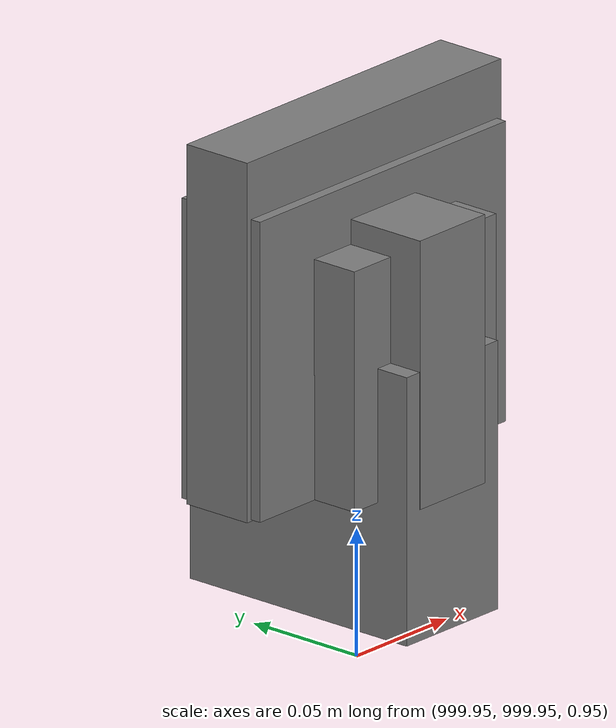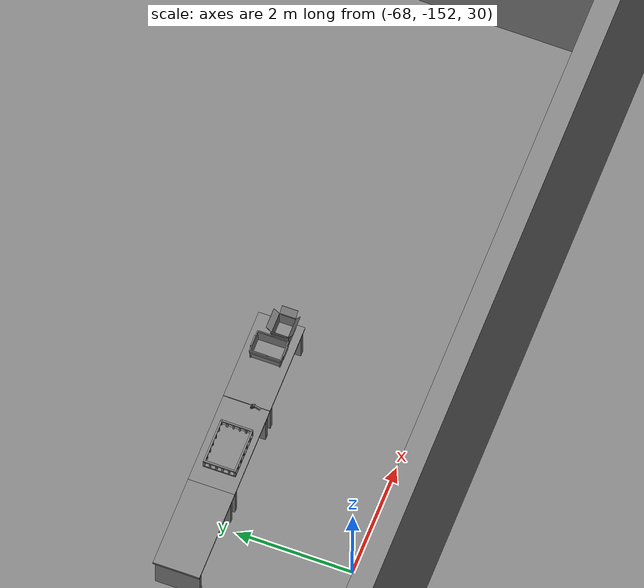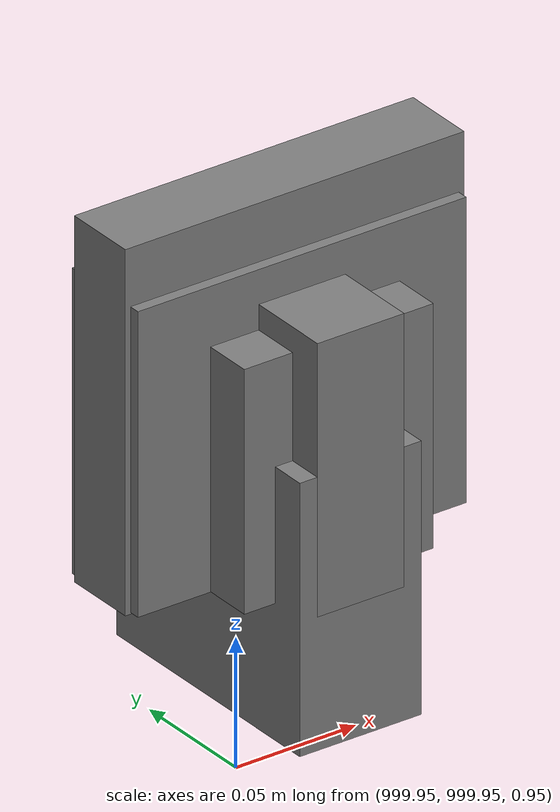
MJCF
<mujoco>
    <option gravity="0.000000000 0.000000000 -9.810000420" timestep="0.0049999999" integrator="implicitfast" density="1.225" viscosity="1.8000001e-05" noslip_iterations="10" iterations="100" sdf_iterations="50">
        <flag multiccd="disable"/>
    </option>
    <size memory="1000M"/>
    <compiler coordinate="local"/>
    <worldbody>
        <light cutoff="30" pos="0 1 1" dir="0 -1 -2"/>
        <light cutoff="30" pos="0 -1 1" dir="0 1 -2"/>
        <body pos="1000.000000000 1000.000000000 1.000000000" euler="0.000000000 0.000000000 180.000000000" name="openloong_gripper_2f85_fix_base_usda_battery_01">
            <geom contype="1" conaffinity="1" density="1000" type="box" material="" rgba="0.500000000 0.500000000 0.500000000 1.000000000" solimp="0.899999976 0.949999988 0.001000000" friction="1.000000000 0.005000000 0.000100000" solref="0.020000000 1.000000000" margin="0" condim="3" group="0" pos="-0.011123657 -0.041940309 0.101691343" quat="1.000000000 0.000000000 0.000000000 0.000000000" size="0.010800000 0.003375000 0.004725000" name="openloong_gripper_2f85_fix_base_usda_geom_F897046C_B270_4CAC_AE00_D35A6BAC4A14"/>
            <geom contype="1" conaffinity="1" density="1000" type="box" material="" rgba="0.500000000 0.500000000 0.500000000 1.000000000" solimp="0.899999976 0.949999988 0.001000000" friction="1.000000000 0.005000000 0.000100000" solref="0.020000000 1.000000000" margin="0" condim="3" group="0" pos="-0.010876465 -0.044247437 0.047066893" quat="0.998702705 -0.050920475 0.000000000 0.000000000" size="0.009450001 0.002700000 0.024975000" name="openloong_gripper_2f85_fix_base_usda_geom_DE0F7B91_EDE6_46A5_AEAB_7E4CC400A1CB"/>
            <geom contype="1" conaffinity="1" density="1000" type="box" material="" rgba="0.500000000 0.500000000 0.500000000 1.000000000" solimp="0.899999976 0.949999988 0.001000000" friction="1.000000000 0.005000000 0.000100000" solref="0.020000000 1.000000000" margin="0" condim="3" group="0" pos="-0.001235962 -0.000659180 0.047381196" quat="1.000000000 0.000000000 0.000000000 0.000000000" size="0.039420001 0.039150000 0.047250003" name="openloong_gripper_2f85_fix_base_usda_geom_9C3ED449_AEB9_43D5_9D42_B0D922ED3078"/>
            <geom contype="1" conaffinity="1" density="1000" type="box" material="" rgba="0.500000000 0.500000000 0.500000000 1.000000000" solimp="0.899999976 0.949999988 0.001000000" friction="1.000000000 0.005000000 0.000100000" solref="0.020000000 1.000000000" margin="0" condim="3" group="0" pos="-0.010876465 -0.039138794 0.009851727" quat="1.000000000 0.000000000 0.000000000 0.000000000" size="0.009450001 0.010800000 0.013500000" name="openloong_gripper_2f85_fix_base_usda_geom_C97370EE_F6AA_4DEB_8D53_810380BFC1A4"/>
            <geom contype="1" conaffinity="1" density="1000" type="box" material="" rgba="0.500000000 0.500000000 0.500000000 1.000000000" solimp="0.899999976 0.949999988 0.001000000" friction="1.000000000 0.005000000 0.000100000" solref="0.020000000 1.000000000" margin="0" condim="3" group="0" pos="-0.010876465 -0.041528322 0.071508206" quat="1.000000000 0.000000000 0.000000000 0.000000000" size="0.009450001 0.002700000 0.027000001" name="openloong_gripper_2f85_fix_base_usda_geom_C257FADD_23EE_45FC_8D87_AEE91377D1D2"/>
            <freejoint name="openloong_gripper_2f85_fix_base_usda_battery_01_joint"/>
            <site size="0.005000000 0.005000000 0.005000000" rgba="0.500000000 0.500000000 0.500000000 1.000000000" pos="0.000000000 0.000000000 0.000000000" quat="0.999961913 0.008726500 0.000000000 0.000000000" group="0" type="sphere" name="openloong_gripper_2f85_fix_base_usda_battery_01site"/>
        </body>
        <body pos="-65.869873047 -149.139297485 31.164909363" euler="-101.674964905 -86.692214966 -85.695808411" mocap="true" name="spotlight3_SpotLight"/>
        <body pos="1000.000000000 1000.000000000 1.000000000" euler="0.000000000 0.000000000 180.000000000" name="openloong_gripper_2f85_fix_base_usda_cpu_fan">
            <geom contype="1" conaffinity="1" density="1000" type="box" material="" rgba="0.500000000 0.500000000 0.500000000 1.000000000" solimp="0.899999976 0.949999988 0.001000000" friction="1.000000000 0.005000000 0.000100000" solref="0.020000000 1.000000000" margin="0" condim="3" group="0" pos="0.000000000 0.000000000 0.070034981" quat="0.000000000 0.000000000 0.000000000 1.000000000" size="0.070700005 0.014699999 0.070700005" name="openloong_gripper_2f85_fix_base_usda_geom_9F205407_AD84_4E8D_8FDB_19224B1AC764"/>
            <freejoint name="openloong_gripper_2f85_fix_base_usda_cpu_fan_joint"/>
            <site size="0.005000000 0.005000000 0.005000000" rgba="0.500000000 0.500000000 0.500000000 1.000000000" pos="0.000000000 0.000000000 0.000000000" quat="0.999961913 0.008726535 0.000000000 0.000000000" group="0" type="sphere" name="openloong_gripper_2f85_fix_base_usda_cpu_fancsite"/>
        </body>
        <body pos="1000.000000000 1000.000000000 1.000000000" euler="0.000000000 0.000000000 180.000000000" name="openloong_gripper_2f85_fix_base_usda_wifi_box">
            <geom contype="1" conaffinity="1" density="1000" type="box" material="" rgba="0.500000000 0.500000000 0.500000000 1.000000000" solimp="0.899999976 0.949999988 0.001000000" friction="1.000000000 0.005000000 0.000100000" solref="0.020000000 1.000000000" margin="0" condim="3" group="0" pos="0.000000000 0.000000000 0.058978677" quat="0.000000000 0.000000047 0.000000000 1.000000000" size="0.068499997 0.018999999 0.059000000" name="openloong_gripper_2f85_fix_base_usda_geom_31082879_0AE1_4E40_9AA6_834265DEA02F"/>
            <freejoint name="openloong_gripper_2f85_fix_base_usda_wifi_box_joint"/>
            <site size="0.005000000 0.005000000 0.005000000" rgba="0.500000000 0.500000000 0.500000000 1.000000000" pos="0.000000000 0.000000000 0.000000000" quat="0.999961913 0.008726500 0.000000000 0.000000000" group="0" type="sphere" name="openloong_gripper_2f85_fix_base_usda_wifi_boxsite"/>
        </body>
        <body pos="1000.000000000 1000.000000000 1.000000000" euler="0.000011953 0.000005123 -179.999984741" name="openloong_gripper_2f85_fix_base_usda_intel_box">
            <geom contype="1" conaffinity="1" density="1000" type="box" material="" rgba="0.500000000 0.500000000 0.500000000 1.000000000" solimp="0.899999976 0.949999988 0.001000000" friction="1.000000000 0.005000000 0.000100000" solref="0.020000000 1.000000000" margin="0" condim="3" group="0" pos="0.000000000 -0.000067139 0.000082284" quat="0.707106709 0.000000225 0.000000253 0.707106650" size="0.052800003 0.025300000 0.052800003" name="openloong_gripper_2f85_fix_base_usda_geom_E113C599_8924_4689_849B_17B947AE94CB"/>
            <freejoint name="openloong_gripper_2f85_fix_base_usda_intel_box_joint"/>
            <site size="0.005000000 0.005000000 0.005000000" rgba="0.500000000 0.500000000 0.500000000 1.000000000" pos="0.000000000 0.000000000 0.000000000" quat="0.999961913 0.008726500 0.000000000 0.000000000" group="0" type="sphere" name="openloong_gripper_2f85_fix_base_usda_intel_boxsite"/>
        </body>
        <body pos="-66.045989990 -149.506164551 31.165412903" euler="165.239471436 27.439548492 -168.021331787" mocap="true" name="spotlight5_SpotLight"/>
        <body pos="1000.000000000 999.999938965 1.000000000" euler="0.000000000 0.000000000 180.000000000" name="openloong_gripper_2f85_fix_base_usda_intelcore_i5">
            <geom contype="1" conaffinity="1" density="1000" type="box" material="" rgba="0.500000000 0.500000000 0.500000000 1.000000000" solimp="0.899999976 0.949999988 0.001000000" friction="1.000000000 0.005000000 0.000100000" solref="0.020000000 1.000000000" margin="0" condim="3" group="0" pos="0.000000000 0.000000000 0.051722717" quat="0.707106709 0.000000000 0.000000000 -0.707106769" size="0.052800000 0.018080002 0.052800000" name="openloong_gripper_2f85_fix_base_usda_geom_3DA46CC5_E70A_4E32_A8E7_76523EDCC115"/>
            <freejoint name="openloong_gripper_2f85_fix_base_usda_intelcore_i5_joint"/>
            <site size="0.005000000 0.005000000 0.005000000" rgba="0.500000000 0.500000000 0.500000000 1.000000000" pos="0.000000000 0.000000000 0.000000000" quat="0.999961913 0.008726534 0.000000000 0.000000000" group="0" type="sphere" name="openloong_gripper_2f85_fix_base_usda_intelcore_i5site"/>
        </body>
        <body pos="-66.214889526 -148.916458130 31.171226501" euler="114.396560669 78.185073853 -34.320529938" mocap="true" name="spotlight2_SpotLight"/>
        <body pos="-64.866622925 -149.383972168 30.183746338" euler="89.999984741 89.999946594 0.000000000" name="openloong_gripper_2f85_fix_base_usda_bluebox_01">
            <geom contype="1" conaffinity="1" density="1000" type="box" material="" rgba="0.500000000 0.500000000 0.500000000 1.000000000" solimp="0.899999976 0.949999988 0.001000000" friction="1.000000000 0.005000000 0.000100000" solref="0.020000000 1.000000000" margin="0" condim="3" group="0" pos="0.276580811 0.187225342 0.000068665" quat="0.707106948 0.000077471 0.707106352 0.000077486" size="0.100000001 0.057999998 0.010000000" name="openloong_gripper_2f85_fix_base_usda_geom_72954F94_5317_427B_99B8_EE2761FC1609"/>
            <geom contype="1" conaffinity="1" density="1000" type="box" material="" rgba="0.500000000 0.500000000 0.500000000 1.000000000" solimp="0.899999976 0.949999988 0.001000000" friction="1.000000000 0.005000000 0.000100000" solref="0.020000000 1.000000000" margin="0" condim="3" group="0" pos="0.000000000 0.002883911 0.000000000" quat="0.999999881 0.000000000 0.000000000 0.000000000" size="0.254000008 0.003000000 0.172000006" name="openloong_gripper_2f85_fix_base_usda_geom_7F0FC0F2_7A82_4C98_9EA5_E31B7B4D8731"/>
            <geom contype="1" conaffinity="1" density="1000" type="box" material="" rgba="0.500000000 0.500000000 0.500000000 1.000000000" solimp="0.899999976 0.949999988 0.001000000" friction="1.000000000 0.005000000 0.000100000" solref="0.020000000 1.000000000" margin="0" condim="3" group="0" pos="0.000000000 0.124874115 0.173484802" quat="0.999796331 0.020176515 -0.000000015 0.000000030" size="0.259999990 0.119999997 0.007000000" name="openloong_gripper_2f85_fix_base_usda_geom_A2DC1405_7EBE_4B6D_97B6_198B1BB7F5A6"/>
            <geom contype="1" conaffinity="1" density="1000" type="box" material="" rgba="0.500000000 0.500000000 0.500000000 1.000000000" solimp="0.899999976 0.949999988 0.001000000" friction="1.000000000 0.005000000 0.000100000" solref="0.020000000 1.000000000" margin="0" condim="3" group="0" pos="0.000000000 0.124874115 -0.173469543" quat="0.999796331 -0.020176545 -0.000000015 0.000000000" size="0.259999990 0.119999997 0.007000000" name="openloong_gripper_2f85_fix_base_usda_geom_7B3A80D4_364B_43BA_90DD_0B42C3DEA2E4"/>
            <geom contype="1" conaffinity="1" density="1000" type="box" material="" rgba="0.500000000 0.500000000 0.500000000 1.000000000" solimp="0.899999976 0.949999988 0.001000000" friction="1.000000000 0.005000000 0.000100000" solref="0.020000000 1.000000000" margin="0" condim="3" group="0" pos="0.000000000 0.214008331 0.188980103" quat="0.999912977 0.013176724 0.000000015 0.000000000" size="0.259999990 0.029999999 0.012500000" name="openloong_gripper_2f85_fix_base_usda_geom_DF09B108_5791_4ECA_BBCD_7D3A78E6E147"/>
            <geom contype="1" conaffinity="1" density="1000" type="box" material="" rgba="0.500000000 0.500000000 0.500000000 1.000000000" solimp="0.899999976 0.949999988 0.001000000" friction="1.000000000 0.005000000 0.000100000" solref="0.020000000 1.000000000" margin="0" condim="3" group="0" pos="-0.258361816 0.125289917 0.001876831" quat="0.702796936 -0.020792112 0.710783124 0.020769298" size="0.189999998 0.119999997 0.009000000" name="openloong_gripper_2f85_fix_base_usda_geom_D6E2F0E1_769B_4AB0_8F2C_60153F164248"/>
            <geom contype="1" conaffinity="1" density="1000" type="box" material="" rgba="0.500000000 0.500000000 0.500000000 1.000000000" solimp="0.899999976 0.949999988 0.001000000" friction="1.000000000 0.005000000 0.000100000" solref="0.020000000 1.000000000" margin="0" condim="3" group="0" pos="0.000000000 0.214008331 -0.188980103" quat="0.999912977 -0.013176769 0.000000030 0.000000015" size="0.259999990 0.029999999 0.012500000" name="openloong_gripper_2f85_fix_base_usda_geom_E0F4C5ED_BC6B_49A3_A55C_BAF025B90E5D"/>
            <geom contype="1" conaffinity="1" density="1000" type="box" material="" rgba="0.500000000 0.500000000 0.500000000 1.000000000" solimp="0.899999976 0.949999988 0.001000000" friction="1.000000000 0.005000000 0.000100000" solref="0.020000000 1.000000000" margin="0" condim="3" group="0" pos="-0.276611328 0.187225342 0.000068665" quat="0.707106650 0.000077441 0.707106709 0.000077456" size="0.100000001 0.057999998 0.010000000" name="openloong_gripper_2f85_fix_base_usda_geom_03F5ECD8_30DB_47B4_A8C5_C6CCC8BEBD42"/>
            <geom contype="1" conaffinity="1" density="1000" type="box" material="" rgba="0.500000000 0.500000000 0.500000000 1.000000000" solimp="0.899999976 0.949999988 0.001000000" friction="1.000000000 0.005000000 0.000100000" solref="0.020000000 1.000000000" margin="0" condim="3" group="0" pos="0.258331299 0.125289917 0.001876831" quat="0.702851415 0.018856421 0.710823774 -0.019329369" size="0.189999998 0.119999997 0.009000000" name="openloong_gripper_2f85_fix_base_usda_geom_83202131_D7C0_4A40_825A_8D022B3E5C0B"/>
            <freejoint name="openloong_gripper_2f85_fix_base_usda_bluebox_01_joint"/>
            <site size="0.005000000 0.005000000 0.005000000" rgba="0.500000000 0.500000000 0.500000000 1.000000000" pos="0.000000000 0.000000000 0.000000000" quat="0.999961913 0.008726534 0.000000000 0.000000000" group="0" type="sphere" name="openloong_gripper_2f85_fix_base_usda_bluebox_01site"/>
        </body>
        <body pos="-64.496299744 -149.491867065 30.235729218" euler="0.000000000 0.000000000 89.999946594" name="openloong_gripper_2f85_fix_base_usda_cardboardbox_01">
            <geom contype="1" conaffinity="1" density="1000" type="box" material="" rgba="0.500000000 0.500000000 0.500000000 1.000000000" solimp="0.899999976 0.949999988 0.001000000" friction="1.000000000 0.005000000 0.000100000" solref="0.020000000 1.000000000" margin="0" condim="3" group="0" pos="-0.003166199 -0.004086494 0.005052090" quat="1.000000000 0.000000000 0.000000000 0.000000000" size="0.142499998 0.177500010 0.005000000" name="openloong_gripper_2f85_fix_base_usda_geom_2B39A2DD_2170_4B5E_8448_E75EB757D134"/>
            <geom contype="1" conaffinity="1" density="1000" type="box" material="" rgba="0.500000000 0.500000000 0.500000000 1.000000000" solimp="0.899999976 0.949999988 0.001000000" friction="1.000000000 0.005000000 0.000100000" solref="0.020000000 1.000000000" margin="0" condim="3" group="0" pos="-0.003166199 0.170316696 0.150570869" quat="1.000000000 0.000000000 0.000000000 0.000000000" size="0.142499998 0.005000000 0.149999991" name="openloong_gripper_2f85_fix_base_usda_geom_76261E29_1442_4824_914E_10224F4BE806"/>
            <geom contype="1" conaffinity="1" density="1000" type="box" material="" rgba="0.500000000 0.500000000 0.500000000 1.000000000" solimp="0.899999976 0.949999988 0.001000000" friction="1.000000000 0.005000000 0.000100000" solref="0.020000000 1.000000000" margin="0" condim="3" group="0" pos="-0.147399902 -0.005307198 0.150570869" quat="1.000000000 0.000000000 0.000000000 0.000000000" size="0.005000000 0.177500010 0.149999991" name="openloong_gripper_2f85_fix_base_usda_geom_D69DF7AF_4277_4781_9BD5_C923C94162B7"/>
            <geom contype="1" conaffinity="1" density="1000" type="box" material="" rgba="0.500000000 0.500000000 0.500000000 1.000000000" solimp="0.899999976 0.949999988 0.001000000" friction="1.000000000 0.005000000 0.000100000" solref="0.020000000 1.000000000" margin="0" condim="3" group="0" pos="0.140275955 -0.005307198 0.150570869" quat="1.000000000 0.000000000 0.000000000 0.000000000" size="0.005000000 0.177500010 0.149999991" name="openloong_gripper_2f85_fix_base_usda_geom_2E333E38_D543_423A_B19C_ED1B8B9594A0"/>
            <geom contype="1" conaffinity="1" density="1000" type="box" material="" rgba="0.500000000 0.500000000 0.500000000 1.000000000" solimp="0.899999976 0.949999988 0.001000000" friction="1.000000000 0.005000000 0.000100000" solref="0.020000000 1.000000000" margin="0" condim="3" group="0" pos="-0.003166199 -0.181550980 0.150570869" quat="1.000000000 0.000000000 0.000000000 0.000000000" size="0.142499998 0.005000000 0.149999991" name="openloong_gripper_2f85_fix_base_usda_geom_BDE804D2_DFDF_49B5_9603_381B114FF12E"/>
            <freejoint name="openloong_gripper_2f85_fix_base_usda_cardboardbox_01_joint"/>
            <site size="0.005000000 0.005000000 0.005000000" rgba="0.500000000 0.500000000 0.500000000 1.000000000" pos="0.000000000 0.000000000 0.000000000" quat="0.999961913 0.008726535 0.000000000 0.000000000" group="0" type="sphere" name="openloong_gripper_2f85_fix_base_usda_site_F5FB5E8B_A0DA_43F0_AF91_7EF68F79C6CA"/>
            <body pos="0.139160156 -0.004048347 0.301930904" euler="-179.999954224 49.383502960 179.999954224" name="openloong_gripper_2f85_fix_base_usda_A1_006">
                <geom contype="1" conaffinity="1" density="1000" type="box" material="" rgba="0.500000000 0.500000000 0.500000000 1.000000000" solimp="0.899999976 0.949999988 0.001000000" friction="1.000000000 0.005000000 0.000100000" solref="0.020000000 1.000000000" margin="0" condim="3" group="0" pos="-0.071587563 0.000009537 0.001745224" quat="0.999999881 0.000000000 0.000000000 0.000000000" size="0.071249999 0.179999992 0.002500000" name="openloong_gripper_2f85_fix_base_usda_geom_2F15D93A_21FD_4CB0_A57F_05C41B569315"/>
                <joint armature="0" stiffness="0.07" damping="0.0099999998" axis="0.000000 1.000000 0.000000" type="hinge" name="openloong_gripper_2f85_fix_base_usda_A1_006"/>
            </body>
            <body pos="-0.145902634 -0.004086494 0.301938057" euler="-180.000000000 -60.000011444 -180.000000000" name="openloong_gripper_2f85_fix_base_usda_A2_006">
                <geom contype="1" conaffinity="1" density="1000" type="box" material="" rgba="0.500000000 0.500000000 0.500000000 1.000000000" solimp="0.899999976 0.949999988 0.001000000" friction="1.000000000 0.005000000 0.000100000" solref="0.020000000 1.000000000" margin="0" condim="3" group="0" pos="0.071268082 0.000009537 0.002717972" quat="0.000002921 0.000000000 -0.000000030 0.999999881" size="0.071249999 0.179999992 0.002500000" name="openloong_gripper_2f85_fix_base_usda_geom_583F1D97_60DC_4397_B880_655EFEF83C61"/>
                <joint armature="0" stiffness="0.07" damping="0.0099999998" axis="0.000000 1.000000 0.000000" type="hinge" name="openloong_gripper_2f85_fix_base_usda_A2_006"/>
            </body>
            <body pos="-0.003385544 0.175991058 0.301930904" euler="-125.858116150 -0.000004561 0.000002331" name="openloong_gripper_2f85_fix_base_usda_B2_006">
                <geom contype="1" conaffinity="1" density="1000" type="box" material="" rgba="0.500000000 0.500000000 0.500000000 1.000000000" solimp="0.899999976 0.949999988 0.001000000" friction="1.000000000 0.005000000 0.000100000" solref="0.020000000 1.000000000" margin="0" condim="3" group="0" pos="0.000009537 -0.070939064 -0.002470016" quat="0.999614120 0.027776197 -0.000000015 0.000000030" size="0.137500003 0.064999998 0.005000000" name="openloong_gripper_2f85_fix_base_usda_geom_1A645E45_E3D9_4B6E_9B33_00B3B522B078"/>
                <joint armature="0" stiffness="0.07" damping="0.0099999998" axis="1.000000 0.000000 0.000000" type="hinge" name="openloong_gripper_2f85_fix_base_usda_B2_006"/>
            </body>
            <body pos="-0.003385544 -0.184140205 0.301938057" euler="147.805557251 0.000000000 0.000000000" name="openloong_gripper_2f85_fix_base_usda_B1_006">
                <geom contype="1" conaffinity="1" density="1000" type="box" material="" rgba="0.500000000 0.500000000 0.500000000 1.000000000" solimp="0.899999976 0.949999988 0.001000000" friction="1.000000000 0.005000000 0.000100000" solref="0.020000000 1.000000000" margin="0" condim="3" group="0" pos="-0.000028610 0.070202351 -0.002703667" quat="0.999614179 -0.027776167 0.000000000 0.000000000" size="0.137500003 0.064999998 0.005000000" name="openloong_gripper_2f85_fix_base_usda_geom_715E4F3E_96AD_423E_8DF0_608A9FF2A808"/>
                <joint armature="0" stiffness="0.07" damping="0.0099999998" axis="1.000000 0.000000 0.000000" type="hinge" name="openloong_gripper_2f85_fix_base_usda_B1_006"/>
            </body>
        </body>
        <body pos="-65.882858276 -149.481979370 30.229999542" euler="-64.487716675 0.000000000 0.000000000" name="openloong_gripper_2f85_fix_base_usda_Barcode">
            <geom contype="1" conaffinity="1" density="1000" type="box" material="" rgba="0.500000000 0.500000000 0.500000000 1.000000000" solimp="0.899999976 0.949999988 0.001000000" friction="1.000000000 0.005000000 0.000100000" solref="0.020000000 1.000000000" margin="0" condim="3" group="0" pos="0.000000000 0.013038635 0.001419067" quat="0.000000000 0.000000000 0.000000000 1.000000119" size="0.034000002 0.010000000 0.017999999" name="openloong_gripper_2f85_fix_base_usda_geom_17AAB37D_C19B_4A87_9417_810D9FC7D30F"/>
            <geom contype="1" conaffinity="1" density="1000" type="box" material="" rgba="0.500000000 0.500000000 0.500000000 1.000000000" solimp="0.899999976 0.949999988 0.001000000" friction="1.000000000 0.005000000 0.000100000" solref="0.020000000 1.000000000" margin="0" condim="3" group="0" pos="0.000000000 -0.035301208 -0.007095337" quat="0.000000000 0.000000000 -0.043619365 0.999048233" size="0.028999999 0.010000000 0.020000000" name="openloong_gripper_2f85_fix_base_usda_geom_06FA40F4_0840_45E3_B0CF_48CC1269B13A"/>
            <geom contype="1" conaffinity="1" density="1000" type="box" material="" rgba="0.500000000 0.500000000 0.500000000 1.000000000" solimp="0.899999976 0.949999988 0.001000000" friction="1.000000000 0.005000000 0.000100000" solref="0.020000000 1.000000000" margin="0" condim="3" group="0" pos="0.000000000 -0.043411255 -0.011749268" quat="0.922262907 0.386563420 0.000000000 0.000000000" size="0.026000001 0.010000000 0.020000000" name="openloong_gripper_2f85_fix_base_usda_geom_B1FC3C5F_C45A_4270_88D1_9C5F7D50EF00"/>
            <geom contype="1" conaffinity="1" density="1000" type="box" material="" rgba="0.500000000 0.500000000 0.500000000 1.000000000" solimp="0.899999976 0.949999988 0.001000000" friction="1.000000000 0.005000000 0.000100000" solref="0.020000000 1.000000000" margin="0" condim="3" group="0" pos="0.000000000 -0.016967773 -0.031860352" quat="0.000000000 0.000000000 0.000000000 1.000000119" size="0.008000000 0.010000000 0.013000000" name="openloong_gripper_2f85_fix_base_usda_geom_A4BA8033_1F9F_413A_A2EB_96B18D68F641"/>
            <geom contype="1" conaffinity="1" density="1000" type="box" material="" rgba="0.500000000 0.500000000 0.500000000 1.000000000" solimp="0.899999976 0.949999988 0.001000000" friction="1.000000000 0.005000000 0.000100000" solref="0.020000000 1.000000000" margin="0" condim="3" group="0" pos="0.000000000 -0.001869202 0.000312805" quat="0.953716993 0.300705761 0.000000000 0.000000000" size="0.032000002 0.010000000 0.018999999" name="openloong_gripper_2f85_fix_base_usda_geom_D3F8A931_23B4_48A0_B621_59003815B043"/>
            <geom contype="1" conaffinity="1" density="1000" type="box" material="" rgba="0.500000000 0.500000000 0.500000000 1.000000000" solimp="0.899999976 0.949999988 0.001000000" friction="1.000000000 0.005000000 0.000100000" solref="0.020000000 1.000000000" margin="0" condim="3" group="0" pos="0.000000000 -0.019531250 -0.003173828" quat="0.953716993 0.300705761 0.000000000 0.000000000" size="0.030999999 0.010000000 0.020000000" name="openloong_gripper_2f85_fix_base_usda_geom_8F9E0564_8D01_4666_AB05_9CBE6991A476"/>
            <geom contype="1" conaffinity="1" density="1000" type="box" material="" rgba="0.500000000 0.500000000 0.500000000 1.000000000" solimp="0.899999976 0.949999988 0.001000000" friction="1.000000000 0.005000000 0.000100000" solref="0.020000000 1.000000000" margin="0" condim="3" group="0" pos="0.000000000 -0.035301208 -0.007095337" quat="0.953716993 0.300705761 0.000000000 0.000000000" size="0.028999999 0.010000000 0.020000000" name="openloong_gripper_2f85_fix_base_usda_geom_3AA2DF57_3666_4E1D_80A4_21162EF8B9D1"/>
            <geom contype="1" conaffinity="1" density="1000" type="box" material="" rgba="0.500000000 0.500000000 0.500000000 1.000000000" solimp="0.899999976 0.949999988 0.001000000" friction="1.000000000 0.005000000 0.000100000" solref="0.020000000 1.000000000" margin="0" condim="3" group="0" pos="0.000000000 -0.042617798 -0.071121216" quat="0.000000000 0.000000000 0.000000000 1.000000119" size="0.013000000 0.021000000 0.059999999" name="openloong_gripper_2f85_fix_base_usda_geom_635EA0C2_D346_40EA_B8A1_FF50452D342F"/>
            <freejoint name="openloong_gripper_2f85_fix_base_usda_Barcode_joint"/>
            <site size="0.005000000 0.005000000 0.005000000" rgba="0.500000000 0.500000000 0.500000000 1.000000000" pos="0.000000000 0.000000000 0.000000000" quat="1.000000000 0.000000000 0.000000000 0.000000000" group="0" type="sphere" name="openloong_gripper_2f85_fix_base_usda_Barcode_site"/>
        </body>
        <body pos="-66.745018005 -149.392349243 30.184000015" euler="0.000000000 0.000000000 89.999946594" name="[22331998244748]_Basket_01">
            <geom contype="1" conaffinity="1" density="1000" type="box" material="" rgba="0.500000000 0.500000000 0.500000000 1.000000000" solimp="0.899999976 0.949999988 0.001000000" friction="1.000000000 0.005000000 0.000100000" solref="0.020000000 1.000000000" margin="0" condim="3" group="0" pos="-0.052425385 0.389207840 0.089787483" quat="0.707107008 0.000000000 0.000000000 0.707106411" size="0.014249999 0.014249999 0.059999999" name="[22331998244748]_geom_AED1DE25_8CA5_4614_ADF7_F314BFDED3D4"/>
            <geom contype="1" conaffinity="1" density="1000" type="box" material="" rgba="0.500000000 0.500000000 0.500000000 1.000000000" solimp="0.899999976 0.949999988 0.001000000" friction="1.000000000 0.005000000 0.000100000" solref="0.020000000 1.000000000" margin="0" condim="3" group="0" pos="0.264015198 -0.133043289 0.089787483" quat="0.707107008 0.000000000 0.000000000 0.707106411" size="0.014249999 0.014249999 0.059999999" name="[22331998244748]_geom_16C02926_7BDB_4077_821E_38D02653E3C2"/>
            <geom contype="1" conaffinity="1" density="1000" type="box" material="" rgba="0.500000000 0.500000000 0.500000000 1.000000000" solimp="0.899999976 0.949999988 0.001000000" friction="1.000000000 0.005000000 0.000100000" solref="0.020000000 1.000000000" margin="0" condim="3" group="0" pos="-0.264015198 -0.265548706 0.089793205" quat="0.707107008 0.000000000 0.000000000 0.707106411" size="0.014249999 0.014249999 0.059999999" name="[22331998244748]_geom_DB271DFD_6CCE_4252_9A2F_A51A8FCFF96D"/>
            <geom contype="1" conaffinity="1" density="1000" type="box" material="" rgba="0.500000000 0.500000000 0.500000000 1.000000000" solimp="0.899999976 0.949999988 0.001000000" friction="1.000000000 0.005000000 0.000100000" solref="0.020000000 1.000000000" margin="0" condim="3" group="0" pos="-0.160263062 -0.389322281 0.089793205" quat="0.707107008 0.000000000 0.000000000 0.707106411" size="0.014249999 0.014249999 0.059999999" name="[22331998244748]_geom_859E2E0C_FCFC_4474_9D33_645418302FA5"/>
            <geom contype="1" conaffinity="1" density="1000" type="box" material="" rgba="0.500000000 0.500000000 0.500000000 1.000000000" solimp="0.899999976 0.949999988 0.001000000" friction="1.000000000 0.005000000 0.000100000" solref="0.020000000 1.000000000" margin="0" condim="3" group="0" pos="0.162265778 -0.389322281 0.089787483" quat="0.707107008 0.000000000 0.000000000 0.707106411" size="0.014249999 0.014249999 0.059999999" name="[22331998244748]_geom_16A11798_20CD_45DE_A485_F594D01784DA"/>
            <geom contype="1" conaffinity="1" density="1000" type="box" material="" rgba="0.500000000 0.500000000 0.500000000 1.000000000" solimp="0.899999976 0.949999988 0.001000000" friction="1.000000000 0.005000000 0.000100000" solref="0.020000000 1.000000000" margin="0" condim="3" group="0" pos="0.264015198 0.389207840 0.089787483" quat="0.707107008 0.000000000 0.000000000 0.707106411" size="0.014249999 0.014249999 0.059999999" name="[22331998244748]_geom_B65D554D_0DD1_461B_A7DF_50326AFC01E1"/>
            <geom contype="1" conaffinity="1" density="1000" type="box" material="" rgba="0.500000000 0.500000000 0.500000000 1.000000000" solimp="0.899999976 0.949999988 0.001000000" friction="1.000000000 0.005000000 0.000100000" solref="0.020000000 1.000000000" margin="0" condim="3" group="0" pos="-0.264015198 -0.133043289 0.089793205" quat="0.707107008 0.000000000 0.000000000 0.707106411" size="0.014249999 0.014249999 0.059999999" name="[22331998244748]_geom_91F5CFF9_913E_41B7_BE73_85CDE2D1D9AD"/>
            <geom contype="1" conaffinity="1" density="1000" type="box" material="" rgba="0.500000000 0.500000000 0.500000000 1.000000000" solimp="0.899999976 0.949999988 0.001000000" friction="1.000000000 0.005000000 0.000100000" solref="0.020000000 1.000000000" margin="0" condim="3" group="0" pos="-0.264026642 0.269256592 0.089793205" quat="0.707107008 0.000000000 0.000000000 0.707106411" size="0.014249999 0.014249999 0.059999999" name="[22331998244748]_geom_6EC453A8_0F0E_4725_89A5_50753BCA7A51"/>
            <geom contype="1" conaffinity="1" density="1000" type="box" material="" rgba="0.500000000 0.500000000 0.500000000 1.000000000" solimp="0.899999976 0.949999988 0.001000000" friction="1.000000000 0.005000000 0.000100000" solref="0.020000000 1.000000000" margin="0" condim="3" group="0" pos="0.054462433 0.389207840 0.089787483" quat="0.707107008 0.000000000 0.000000000 0.707106411" size="0.014249999 0.014249999 0.059999999" name="[22331998244748]_geom_9B56481E_B53E_4E9E_A01D_4CB86ABF2979"/>
            <geom contype="1" conaffinity="1" density="1000" type="box" material="" rgba="0.500000000 0.500000000 0.500000000 1.000000000" solimp="0.899999976 0.949999988 0.001000000" friction="1.000000000 0.005000000 0.000100000" solref="0.020000000 1.000000000" margin="0" condim="3" group="0" pos="0.054462433 -0.389322281 0.089787483" quat="0.707107008 0.000000000 0.000000000 0.707106411" size="0.014249999 0.014249999 0.059999999" name="[22331998244748]_geom_67AA8775_385F_41F6_910D_05B95D85C620"/>
            <geom contype="1" conaffinity="1" density="1000" type="box" material="" rgba="0.500000000 0.500000000 0.500000000 1.000000000" solimp="0.899999976 0.949999988 0.001000000" friction="1.000000000 0.005000000 0.000100000" solref="0.020000000 1.000000000" margin="0" condim="3" group="0" pos="0.264015198 0.269256592 0.089793205" quat="0.707107008 0.000000000 0.000000000 0.707106411" size="0.014249999 0.014249999 0.059999999" name="[22331998244748]_geom_C0E228C3_2D58_40FE_9C2F_8AFD4886A680"/>
            <geom contype="1" conaffinity="1" density="1000" type="box" material="" rgba="0.500000000 0.500000000 0.500000000 1.000000000" solimp="0.899999976 0.949999988 0.001000000" friction="1.000000000 0.005000000 0.000100000" solref="0.020000000 1.000000000" margin="0" condim="3" group="0" pos="0.264015198 -0.389322281 0.089787483" quat="0.707107008 0.000000000 0.000000000 0.707106411" size="0.014249999 0.014249999 0.059999999" name="[22331998244748]_geom_EF4ED146_0F85_49BE_8528_2AAE0744367A"/>
            <geom contype="1" conaffinity="1" density="1000" type="box" material="" rgba="0.500000000 0.500000000 0.500000000 1.000000000" solimp="0.899999976 0.949999988 0.001000000" friction="1.000000000 0.005000000 0.000100000" solref="0.020000000 1.000000000" margin="0" condim="3" group="0" pos="0.000000000 0.000000000 0.015998840" quat="0.707107008 0.000000000 0.000000000 0.707106411" size="0.403499991 0.279000014 0.015750000" name="[22331998244748]_geom_03E298BD_5F3D_4DD9_A21F_83136A6658B9"/>
            <geom contype="1" conaffinity="1" density="1000" type="box" material="" rgba="0.500000000 0.500000000 0.500000000 1.000000000" solimp="0.899999976 0.949999988 0.001000000" friction="1.000000000 0.005000000 0.000100000" solref="0.020000000 1.000000000" margin="0" condim="3" group="0" pos="0.000000000 -0.389476776 0.163619041" quat="0.707107008 0.000000000 0.000000000 0.707106411" size="0.015000000 0.277500004 0.015750000" name="[22331998244748]_geom_8B68FF0A_65C9_4947_8A85_0C77BB5876B8"/>
            <geom contype="1" conaffinity="1" density="1000" type="box" material="" rgba="0.500000000 0.500000000 0.500000000 1.000000000" solimp="0.899999976 0.949999988 0.001000000" friction="1.000000000 0.005000000 0.000100000" solref="0.020000000 1.000000000" margin="0" condim="3" group="0" pos="0.162265778 0.389207840 0.089787483" quat="0.707107008 0.000000000 0.000000000 0.707106411" size="0.014249999 0.014249999 0.059999999" name="[22331998244748]_geom_317AB714_09B8_4D36_AEE2_A8E51A41D3C3"/>
            <geom contype="1" conaffinity="1" density="1000" type="box" material="" rgba="0.500000000 0.500000000 0.500000000 1.000000000" solimp="0.899999976 0.949999988 0.001000000" friction="1.000000000 0.005000000 0.000100000" solref="0.020000000 1.000000000" margin="0" condim="3" group="0" pos="0.000000000 0.389471054 0.163619041" quat="0.707107008 0.000000000 0.000000000 0.707106411" size="0.015000000 0.277500004 0.015750000" name="[22331998244748]_geom_ACCCD3F4_986C_4ED5_A792_B565A6552134"/>
            <geom contype="1" conaffinity="1" density="1000" type="box" material="" rgba="0.500000000 0.500000000 0.500000000 1.000000000" solimp="0.899999976 0.949999988 0.001000000" friction="1.000000000 0.005000000 0.000100000" solref="0.020000000 1.000000000" margin="0" condim="3" group="0" pos="-0.263511658 0.000000000 0.163619041" quat="0.707107008 0.000000000 0.000000000 0.707106411" size="0.403499991 0.015000000 0.015750000" name="[22331998244748]_geom_F99C4FA0_2426_436F_B2AF_8F92D34EEF72"/>
            <geom contype="1" conaffinity="1" density="1000" type="box" material="" rgba="0.500000000 0.500000000 0.500000000 1.000000000" solimp="0.899999976 0.949999988 0.001000000" friction="1.000000000 0.005000000 0.000100000" solref="0.020000000 1.000000000" margin="0" condim="3" group="0" pos="-0.264015198 0.141334534 0.089793205" quat="0.707107008 0.000000000 0.000000000 0.707106411" size="0.014249999 0.014249999 0.059999999" name="[22331998244748]_geom_CEAC50C2_528B_4F0B_9313_3B7CFA588577"/>
            <geom contype="1" conaffinity="1" density="1000" type="box" material="" rgba="0.500000000 0.500000000 0.500000000 1.000000000" solimp="0.899999976 0.949999988 0.001000000" friction="1.000000000 0.005000000 0.000100000" solref="0.020000000 1.000000000" margin="0" condim="3" group="0" pos="0.264015198 -0.265548706 0.089787483" quat="0.707107008 0.000000000 0.000000000 0.707106411" size="0.014249999 0.014249999 0.059999999" name="[22331998244748]_geom_54737FAB_6F0D_4E69_A1DC_588F63ECC9A4"/>
            <geom contype="1" conaffinity="1" density="1000" type="box" material="" rgba="0.500000000 0.500000000 0.500000000 1.000000000" solimp="0.899999976 0.949999988 0.001000000" friction="1.000000000 0.005000000 0.000100000" solref="0.020000000 1.000000000" margin="0" condim="3" group="0" pos="-0.160263062 0.389207840 0.089787483" quat="0.707107008 0.000000000 0.000000000 0.707106411" size="0.014249999 0.014249999 0.059999999" name="[22331998244748]_geom_3A61564C_208B_4BD3_829A_9501BECE732C"/>
            <geom contype="1" conaffinity="1" density="1000" type="box" material="" rgba="0.500000000 0.500000000 0.500000000 1.000000000" solimp="0.899999976 0.949999988 0.001000000" friction="1.000000000 0.005000000 0.000100000" solref="0.020000000 1.000000000" margin="0" condim="3" group="0" pos="-0.052425385 -0.389322281 0.089787483" quat="0.707107008 0.000000000 0.000000000 0.707106411" size="0.014249999 0.014249999 0.059999999" name="[22331998244748]_geom_7A305DD2_BCE8_4BCB_ACD5_36BB66862B21"/>
            <geom contype="1" conaffinity="1" density="1000" type="box" material="" rgba="0.500000000 0.500000000 0.500000000 1.000000000" solimp="0.899999976 0.949999988 0.001000000" friction="1.000000000 0.005000000 0.000100000" solref="0.020000000 1.000000000" margin="0" condim="3" group="0" pos="-0.264026642 -0.389322281 0.089793205" quat="0.707107008 0.000000000 0.000000000 0.707106411" size="0.014249999 0.014249999 0.059999999" name="[22331998244748]_geom_0F048BE7_69AA_4551_9811_4595FE38AA95"/>
            <geom contype="1" conaffinity="1" density="1000" type="box" material="" rgba="0.500000000 0.500000000 0.500000000 1.000000000" solimp="0.899999976 0.949999988 0.001000000" friction="1.000000000 0.005000000 0.000100000" solref="0.020000000 1.000000000" margin="0" condim="3" group="0" pos="0.264015198 0.141334534 0.089787483" quat="0.707107008 0.000000000 0.000000000 0.707106411" size="0.014249999 0.014249999 0.059999999" name="[22331998244748]_geom_9332163E_A115_4E53_8140_4750E9498B20"/>
            <geom contype="1" conaffinity="1" density="1000" type="box" material="" rgba="0.500000000 0.500000000 0.500000000 1.000000000" solimp="0.899999976 0.949999988 0.001000000" friction="1.000000000 0.005000000 0.000100000" solref="0.020000000 1.000000000" margin="0" condim="3" group="0" pos="-0.264015198 0.389207840 0.089793205" quat="0.707107008 0.000000000 0.000000000 0.707106411" size="0.014249999 0.014249999 0.059999999" name="[22331998244748]_geom_D5EA9355_D801_45FF_B26A_3A7502B6CB1A"/>
            <geom contype="1" conaffinity="1" density="1000" type="box" material="" rgba="0.500000000 0.500000000 0.500000000 1.000000000" solimp="0.899999976 0.949999988 0.001000000" friction="1.000000000 0.005000000 0.000100000" solref="0.020000000 1.000000000" margin="0" condim="3" group="0" pos="0.264015198 0.004480362 0.089787483" quat="0.707107008 0.000000000 0.000000000 0.707106411" size="0.014249999 0.014249999 0.059999999" name="[22331998244748]_geom_109A79B0_AB1D_46B4_8D98_D37CEAB0E74B"/>
            <geom contype="1" conaffinity="1" density="1000" type="box" material="" rgba="0.500000000 0.500000000 0.500000000 1.000000000" solimp="0.899999976 0.949999988 0.001000000" friction="1.000000000 0.005000000 0.000100000" solref="0.020000000 1.000000000" margin="0" condim="3" group="0" pos="0.263694763 -0.000011444 0.163619041" quat="0.707107008 0.000000000 0.000000000 0.707106411" size="0.403499991 0.015000000 0.015750000" name="[22331998244748]_geom_357483B4_7DE3_41C2_9D50_AF46CFFF07B4"/>
            <geom contype="1" conaffinity="1" density="1000" type="box" material="" rgba="0.500000000 0.500000000 0.500000000 1.000000000" solimp="0.899999976 0.949999988 0.001000000" friction="1.000000000 0.005000000 0.000100000" solref="0.020000000 1.000000000" margin="0" condim="3" group="0" pos="-0.264015198 0.004480362 0.089793205" quat="0.707107008 0.000000000 0.000000000 0.707106411" size="0.014249999 0.014249999 0.059999999" name="[22331998244748]_geom_D029EABA_BB02_4FDE_93E5_45BBE9043D36"/>
            <freejoint name="[22331998244748]_joint_4CC0F355_D339_4C8B_AF86_74825321D910"/>
        </body>
        <body pos="0.000000000 0.000000000 0.000000000" euler="0.000000000 0.000000000 0.000000000" name="Static Objects_Static Objects">
            <geom contype="1" conaffinity="1" density="1000" type="box" material="" rgba="0.500000000 0.500000000 0.500000000 1.000000000" solimp="0.899999976 0.949999988 0.001000000" friction="1.000000000 0.005000000 0.000100000" solref="0.020000000 1.000000000" margin="0" condim="3" group="0" pos="-67.544113159 -149.365814209 29.727830887" quat="0.500000417 0.499999970 0.499999553 0.499999970" size="0.381000012 0.319999993 0.041000001" name="Static Objects_geom_A9296FCB_C7D6_401A_8E6A_F263BECF56B8"/>
            <geom contype="1" conaffinity="1" density="1000" type="box" material="" rgba="0.500000000 0.500000000 0.500000000 1.000000000" solimp="0.899999976 0.949999988 0.001000000" friction="1.000000000 0.005000000 0.000100000" solref="0.020000000 1.000000000" margin="0" condim="3" group="0" pos="-68.239501953 -149.365814209 30.086868286" quat="0.500000417 0.499999970 0.499999553 0.499999970" size="0.370999992 0.039500002 0.745000005" name="Static Objects_geom_C8B74BCE_61EA_4D4D_822C_C5682DE2FE81"/>
            <geom contype="1" conaffinity="1" density="1000" type="box" material="" rgba="0.500000000 0.500000000 0.500000000 1.000000000" solimp="0.899999976 0.949999988 0.001000000" friction="1.000000000 0.005000000 0.000100000" solref="0.020000000 1.000000000" margin="0" condim="3" group="0" pos="-68.239501953 -149.365814209 30.147235870" quat="0.500000417 0.499999970 0.499999553 0.499999970" size="0.400000006 0.022000000 0.800000012" name="Static Objects_geom_B068D132_A669_4E2B_8798_699132ABEE7E"/>
            <geom contype="1" conaffinity="1" density="1000" type="box" material="" rgba="0.500000000 0.500000000 0.500000000 1.000000000" solimp="0.899999976 0.949999988 0.001000000" friction="1.000000000 0.005000000 0.000100000" solref="0.020000000 1.000000000" margin="0" condim="3" group="0" pos="-68.934890747 -149.365814209 29.727830887" quat="0.500000417 0.499999970 0.499999553 0.499999970" size="0.381000012 0.319999993 0.041000001" name="Static Objects_geom_E154790D_CDF4_4B7D_9582_7B0F4C4691DB"/>
            <geom contype="1" conaffinity="1" density="1000" type="box" material="" rgba="0.500000000 0.500000000 0.500000000 1.000000000" solimp="0.899999976 0.949999988 0.001000000" friction="1.000000000 0.005000000 0.000100000" solref="0.020000000 1.000000000" margin="0" condim="3" group="0" pos="-68.239501953 -149.365814209 29.561563492" quat="0.500000417 0.499999970 0.499999553 0.499999970" size="0.020000000 0.022000000 0.660000026" name="Static Objects_geom_CFCFC09D_7F41_475C_9E0C_6CBF38089F14"/>
            <geom contype="1" conaffinity="1" density="1000" type="box" material="" rgba="0.500000000 0.500000000 0.500000000 1.000000000" solimp="0.899999976 0.949999988 0.001000000" friction="1.000000000 0.005000000 0.000100000" solref="0.020000000 1.000000000" margin="0" condim="3" group="0" pos="-65.945671082 -149.365814209 29.727830887" quat="0.500000417 0.499999970 0.499999553 0.499999970" size="0.381000012 0.319999993 0.041000001" name="Static Objects_geom_67C1DFDB_C130_428A_9598_12923AC02B9A"/>
            <geom contype="1" conaffinity="1" density="1000" type="box" material="" rgba="0.500000000 0.500000000 0.500000000 1.000000000" solimp="0.899999976 0.949999988 0.001000000" friction="1.000000000 0.005000000 0.000100000" solref="0.020000000 1.000000000" margin="0" condim="3" group="0" pos="-66.641059875 -149.365814209 30.086868286" quat="0.500000417 0.499999970 0.499999553 0.499999970" size="0.370999992 0.039500002 0.745000005" name="Static Objects_geom_AB87BE74_823F_482E_A28C_F35658F40AFD"/>
            <geom contype="1" conaffinity="1" density="1000" type="box" material="" rgba="0.500000000 0.500000000 0.500000000 1.000000000" solimp="0.899999976 0.949999988 0.001000000" friction="1.000000000 0.005000000 0.000100000" solref="0.020000000 1.000000000" margin="0" condim="3" group="0" pos="-66.641059875 -149.365814209 30.147235870" quat="0.500000417 0.499999970 0.499999553 0.499999970" size="0.400000006 0.022000000 0.800000012" name="Static Objects_geom_A7EF254B_0A39_45FB_917E_E502C51DDB37"/>
            <geom contype="1" conaffinity="1" density="1000" type="box" material="" rgba="0.500000000 0.500000000 0.500000000 1.000000000" solimp="0.899999976 0.949999988 0.001000000" friction="1.000000000 0.005000000 0.000100000" solref="0.020000000 1.000000000" margin="0" condim="3" group="0" pos="-67.336448669 -149.365814209 29.727830887" quat="0.500000417 0.499999970 0.499999553 0.499999970" size="0.381000012 0.319999993 0.041000001" name="Static Objects_geom_1FE6223A_B6DC_458E_9B10_4E6D1CB42D99"/>
            <geom contype="1" conaffinity="1" density="1000" type="box" material="" rgba="0.500000000 0.500000000 0.500000000 1.000000000" solimp="0.899999976 0.949999988 0.001000000" friction="1.000000000 0.005000000 0.000100000" solref="0.020000000 1.000000000" margin="0" condim="3" group="0" pos="-66.641059875 -149.365814209 29.561563492" quat="0.500000417 0.499999970 0.499999553 0.499999970" size="0.020000000 0.022000000 0.660000026" name="Static Objects_geom_E12B6568_D6D7_4524_BAF5_812D4E25FD08"/>
            <geom contype="1" conaffinity="1" density="1000" type="box" material="" rgba="0.500000000 0.500000000 0.500000000 1.000000000" solimp="0.899999976 0.949999988 0.001000000" friction="1.000000000 0.005000000 0.000100000" solref="0.020000000 1.000000000" margin="0" condim="3" group="0" pos="-64.338577271 -149.365814209 29.727830887" quat="0.500000417 0.499999970 0.499999553 0.499999970" size="0.381000012 0.319999993 0.041000001" name="Static Objects_geom_5B108719_356E_4970_BEF6_ACD36C835E79"/>
            <geom contype="1" conaffinity="1" density="1000" type="box" material="" rgba="0.500000000 0.500000000 0.500000000 1.000000000" solimp="0.899999976 0.949999988 0.001000000" friction="1.000000000 0.005000000 0.000100000" solref="0.020000000 1.000000000" margin="0" condim="3" group="0" pos="-65.033966064 -149.365814209 30.086868286" quat="0.500000417 0.499999970 0.499999553 0.499999970" size="0.370999992 0.039500002 0.745000005" name="Static Objects_geom_E64A8993_8586_420F_B401_6FFB42185E25"/>
            <geom contype="1" conaffinity="1" density="1000" type="box" material="" rgba="0.500000000 0.500000000 0.500000000 1.000000000" solimp="0.899999976 0.949999988 0.001000000" friction="1.000000000 0.005000000 0.000100000" solref="0.020000000 1.000000000" margin="0" condim="3" group="0" pos="-65.033966064 -149.365814209 30.147235870" quat="0.500000417 0.499999970 0.499999553 0.499999970" size="0.400000006 0.022000000 0.800000012" name="Static Objects_geom_52EC9F14_C925_421E_AC4E_7477E0E1B2AE"/>
            <geom contype="1" conaffinity="1" density="1000" type="box" material="" rgba="0.500000000 0.500000000 0.500000000 1.000000000" solimp="0.899999976 0.949999988 0.001000000" friction="1.000000000 0.005000000 0.000100000" solref="0.020000000 1.000000000" margin="0" condim="3" group="0" pos="-65.729354858 -149.365814209 29.727830887" quat="0.500000417 0.499999970 0.499999553 0.499999970" size="0.381000012 0.319999993 0.041000001" name="Static Objects_geom_1B0444D8_02EF_4187_B4D3_4F6460A0A9C6"/>
            <geom contype="1" conaffinity="1" density="1000" type="box" material="" rgba="0.500000000 0.500000000 0.500000000 1.000000000" solimp="0.899999976 0.949999988 0.001000000" friction="1.000000000 0.005000000 0.000100000" solref="0.020000000 1.000000000" margin="0" condim="3" group="0" pos="-65.033966064 -149.365814209 29.561563492" quat="0.500000417 0.499999970 0.499999553 0.499999970" size="0.020000000 0.022000000 0.660000026" name="Static Objects_geom_6091CF06_6782_4DA3_B8BB_127828D61B8A"/>
            <geom contype="1" conaffinity="1" density="1000" type="box" material="" rgba="0.500000000 0.500000000 0.500000000 1.000000000" solimp="0.899999976 0.949999988 0.001000000" friction="1.000000000 0.005000000 0.000100000" solref="0.020000000 1.000000000" margin="0" condim="3" group="0" pos="-61.754566193 -137.853729248 33.906845093" quat="0.707107067 0.000000000 0.000000000 0.707106471" size="0.759999990 0.759999990 4.500000000" name="Static Objects_geom_9E0D4F45_5C62_4193_96FD_8B740502DD3F"/>
            <geom contype="1" conaffinity="1" density="1000" type="box" material="" rgba="0.500000000 0.500000000 0.500000000 1.000000000" solimp="0.899999976 0.949999988 0.001000000" friction="1.000000000 0.005000000 0.000100000" solref="0.020000000 1.000000000" margin="0" condim="3" group="0" pos="-57.511135101 -144.927108765 31.707921982" quat="1.000000000 0.000000000 0.000000000 0.000000000" size="0.200000003 8.000000000 2.299999952" name="Static Objects_geom_05B59669_0FA6_498D_859B_471A224D7339"/>
            <geom contype="1" conaffinity="1" density="1000" type="box" material="" rgba="0.500000000 0.500000000 0.500000000 1.000000000" solimp="0.899999976 0.949999988 0.001000000" friction="1.000000000 0.005000000 0.000100000" solref="0.020000000 1.000000000" margin="0" condim="3" group="0" pos="-80.517646790 -157.574050903 31.688196182" quat="0.707107067 0.000000000 0.000000000 0.707106471" size="0.600000024 0.600000024 2.299999952" name="Static Objects_geom_96630BE2_1726_4639_9A03_2FA83200ED86"/>
            <geom contype="1" conaffinity="1" density="1000" type="box" material="" rgba="0.500000000 0.500000000 0.500000000 1.000000000" solimp="0.899999976 0.949999988 0.001000000" friction="1.000000000 0.005000000 0.000100000" solref="0.020000000 1.000000000" margin="0" condim="3" group="0" pos="-80.711044312 -147.414932251 31.666158676" quat="1.000000000 0.000000000 0.000000000 0.000000000" size="0.200000003 10.000000000 2.299999952" name="Static Objects_geom_AFC67C0E_EE3F_461F_8ACD_9309EF2F1FFD"/>
            <geom contype="1" conaffinity="1" density="1000" type="box" material="" rgba="0.500000000 0.500000000 0.500000000 1.000000000" solimp="0.899999976 0.949999988 0.001000000" friction="1.000000000 0.005000000 0.000100000" solref="0.020000000 1.000000000" margin="0" condim="3" group="0" pos="-57.687217712 -137.434692383 31.688196182" quat="0.707107067 0.000000000 0.000000000 0.707106471" size="0.600000024 0.600000024 2.299999952" name="Static Objects_geom_31C31EB6_51D6_4A7C_B0C9_FE1D9BBD6705"/>
            <geom contype="1" conaffinity="1" density="1000" type="box" material="" rgba="0.500000000 0.500000000 0.500000000 1.000000000" solimp="0.899999976 0.949999988 0.001000000" friction="1.000000000 0.005000000 0.000100000" solref="0.020000000 1.000000000" margin="0" condim="3" group="0" pos="-69.537033081 -140.263229370 31.714921951" quat="0.707107067 0.000000000 0.000000000 0.707106471" size="0.759999990 4.500000000 2.299999952" name="Static Objects_geom_13F29336_787D_4EB2_9E53_78CB890B3BD9"/>
            <geom contype="1" conaffinity="1" density="1000" type="box" material="" rgba="0.500000000 0.500000000 0.500000000 1.000000000" solimp="0.899999976 0.949999988 0.001000000" friction="1.000000000 0.005000000 0.000100000" solref="0.020000000 1.000000000" margin="0" condim="3" group="0" pos="-80.073638916 -137.853713989 33.906845093" quat="0.707107067 0.000000000 0.000000000 0.707106471" size="0.759999990 0.759999990 4.500000000" name="Static Objects_geom_D7A8DF0F_EB75_47DF_B38E_F65268A663A3"/>
            <geom contype="1" conaffinity="1" density="1000" type="box" material="" rgba="0.500000000 0.500000000 0.500000000 1.000000000" solimp="0.899999976 0.949999988 0.001000000" friction="1.000000000 0.005000000 0.000100000" solref="0.020000000 1.000000000" margin="0" condim="3" group="0" pos="-73.406707764 -155.734664917 31.707921982" quat="1.000000000 0.000000000 0.000000000 0.000000000" size="0.200000003 3.000000000 2.299999952" name="Static Objects_geom_AAEEB53F_7D16_4CBC_94CE_6977F7095FA8"/>
            <geom contype="1" conaffinity="1" density="1000" type="box" material="" rgba="0.500000000 0.500000000 0.500000000 1.000000000" solimp="0.899999976 0.949999988 0.001000000" friction="1.000000000 0.005000000 0.000100000" solref="0.020000000 1.000000000" margin="0" condim="3" group="0" pos="-68.497543335 -137.448257446 31.707921982" quat="0.707107067 0.000000000 0.000000000 0.707106471" size="0.200000003 14.000000000 2.299999952" name="Static Objects_geom_FD40A57B_4209_4235_962D_2B690BFF5309"/>
            <geom contype="1" conaffinity="1" density="1000" type="cylinder" material="" rgba="0.500000000 0.500000000 0.500000000 1.000000000" solimp="0.899999976 0.949999988 0.001000000" friction="1.000000000 0.005000000 0.000100000" solref="0.020000000 1.000000000" margin="0" condim="3" group="0" pos="-68.868522644 -142.134506226 31.711090088" quat="0.707107067 0.000000000 0.000000000 0.707106471" size="0.509999990 2.299999952 1.000000000" name="Static Objects_geom_FC8F219E_6857_410A_8720_75D66B3F2F38"/>
            <geom contype="1" conaffinity="1" density="1000" type="plane" material="" rgba="0.500000000 0.500000000 0.500000000 1.000000000" solimp="0.899999976 0.949999988 0.001000000" friction="1.000000000 0.005000000 0.000100000" solref="0.020000000 1.000000000" margin="0" condim="3" group="0" pos="-72.873703003 -147.131927490 29.409669876" quat="1.000000000 0.000000000 0.000000000 0.000000000" size="18.000000000 14.000000000 1.000000000" name="Static Objects_geom_E16C882E_9C44_4E8F_925B_2272BBE91636"/>
            <geom contype="1" conaffinity="1" density="1000" type="box" material="" rgba="0.500000000 0.500000000 0.500000000 1.000000000" solimp="0.899999976 0.949999988 0.001000000" friction="1.000000000 0.005000000 0.000100000" solref="0.020000000 1.000000000" margin="0" condim="3" group="0" pos="-79.943580627 -157.782272339 31.707921982" quat="0.707107067 0.000000000 0.000000000 0.707106471" size="0.200000003 7.000000000 2.299999952" name="Static Objects_geom_86716983_15DD_45F3_B808_B6B492F73BE9"/>
            <geom contype="1" conaffinity="1" density="1000" type="box" material="" rgba="0.500000000 0.500000000 0.500000000 1.000000000" solimp="0.899999976 0.949999988 0.001000000" friction="1.000000000 0.005000000 0.000100000" solref="0.020000000 1.000000000" margin="0" condim="3" group="0" pos="-65.421028137 -152.903442383 31.707921982" quat="0.707107067 0.000000000 0.000000000 0.707106471" size="0.200000003 7.800000191 2.299999952" name="Static Objects_geom_7E13D9F7_9FB5_4C10_A146_4353C382BB8C"/>
            <geom contype="1" conaffinity="1" density="1000" type="box" material="" rgba="0.500000000 0.500000000 0.500000000 1.000000000" solimp="0.899999976 0.949999988 0.001000000" friction="1.000000000 0.005000000 0.000100000" solref="0.020000000 1.000000000" margin="0" condim="3" group="0" pos="-74.776908875 -149.964416504 31.688196182" quat="1.000000000 0.000000000 0.000000000 0.000000000" size="0.600000024 0.409999996 2.299999952" name="Static Objects_geom_89C547DD_6003_4EBA_9A82_BB5CB6DC1E39"/>
            <geom contype="1" conaffinity="1" density="1000" type="cylinder" material="" rgba="0.500000000 0.500000000 0.500000000 1.000000000" solimp="0.899999976 0.949999988 0.001000000" friction="1.000000000 0.005000000 0.000100000" solref="0.020000000 1.000000000" margin="0" condim="3" group="0" pos="-60.161884308 -142.134506226 31.711090088" quat="0.707107067 0.000000000 0.000000000 0.707106471" size="0.509999990 2.299999952 1.000000000" name="Static Objects_geom_0BB50DEB_CC69_414B_A0C4_1157E505387D"/>
            <geom contype="1" conaffinity="1" density="1000" type="cylinder" material="" rgba="0.500000000 0.500000000 0.500000000 1.000000000" solimp="0.899999976 0.949999988 0.001000000" friction="1.000000000 0.005000000 0.000100000" solref="0.020000000 1.000000000" margin="0" condim="3" group="0" pos="-75.382453918 -149.963455200 31.711090088" quat="0.707107067 0.000000000 0.000000000 0.707106471" size="0.409999996 2.299999952 1.000000000" name="Static Objects_geom_1025BA30_B147_4396_8ED7_5F90590DEAEF"/>
            <geom contype="1" conaffinity="1" density="1000" type="cylinder" material="" rgba="0.500000000 0.500000000 0.500000000 1.000000000" solimp="0.899999976 0.949999988 0.001000000" friction="1.000000000 0.005000000 0.000100000" solref="0.020000000 1.000000000" margin="0" condim="3" group="0" pos="-74.154960632 -149.963455200 31.711090088" quat="0.707107067 0.000000000 0.000000000 0.707106471" size="0.409999996 2.299999952 1.000000000" name="Static Objects_geom_C9B89D21_4278_4796_9D5E_93B950FFD341"/>
            <geom contype="1" conaffinity="1" density="1000" type="cylinder" material="" rgba="0.500000000 0.500000000 0.500000000 1.000000000" solimp="0.899999976 0.949999988 0.001000000" friction="1.000000000 0.005000000 0.000100000" solref="0.020000000 1.000000000" margin="0" condim="3" group="0" pos="-77.566612244 -142.134506226 31.711090088" quat="0.707107067 0.000000000 0.000000000 0.707106471" size="0.509999990 2.299999952 1.000000000" name="Static Objects_geom_2FEE3551_7BD0_4DFF_A695_277FEFA25984"/>
        </body>
        <body pos="-66.291030884 -149.869689941 29.018842697" euler="0.000000000 0.000000000 89.999946594" mocap="true" name="openloong_gripper_2f85_fix_base_usda_leftHandMocap"/>
        <body pos="-66.291030884 -149.869689941 29.018842697" euler="0.000000000 0.000000000 89.999946594" mocap="true" name="openloong_gripper_2f85_fix_base_usda_rightHandMocap"/>
        <body pos="-66.291030884 -149.869689941 30.218843460" euler="0.000000000 0.000000000 89.999946594" name="openloong_gripper_2f85_fix_base_usda_base_link">
            <geom contype="1" conaffinity="1" density="1000" type="mesh" material="" rgba="0.783999979 0.783999979 0.783999979 1.000000000" solimp="0.899999976 0.949999988 0.001000000" friction="1.000000000 0.005000000 0.000100000" solref="0.020000000 1.000000000" margin="0" condim="3" group="3" mesh="base_link" pos="0.000000000 0.000000000 0.000000000" quat="1.000000000 0.000000000 0.000000000 0.000000000" size="1.000000000 1.000000000 1.000000000" name="openloong_gripper_2f85_fix_base_usda__geom_7_BEE6BF2C_FC13_40AE_8C33_2305561A8FB8"/>
            <site size="0.005000000 0.005000000 0.005000000" rgba="0.500000000 0.500000000 0.500000000 1.000000000" pos="0.000000000 0.000000000 0.000000000" quat="1.000000000 0.000000000 0.000000000 0.000000000" group="0" type="sphere" name="openloong_gripper_2f85_fix_base_usda_imu"/>
            <inertial mass="22.447001" pos="-0.005664100 -0.001336700 0.238289997" diaginertia="0.374352545 0.277180195 0.220617250" quat="0.999247074 0.035235517 -0.015086859 0.006023135"/>
            <body pos="0.000000000 0.000000000 0.299997330" euler="0.000000000 0.000000000 0.000000000" name="openloong_gripper_2f85_fix_base_usda_dummy_body">
                <geom contype="1" conaffinity="1" density="1000" type="sphere" material="" rgba="0.783999979 0.783999979 0.783999979 1.000000000" solimp="0.899999976 0.949999988 0.001000000" friction="1.000000000 0.005000000 0.000100000" solref="0.020000000 1.000000000" margin="0" condim="3" group="3" pos="0.000000000 0.000000000 0.000000000" quat="1.000000000 0.000000000 0.000000000 0.000000000" size="0.010000000 0.000000000 0.000000000" name="openloong_gripper_2f85_fix_base_usda__geom_8_6B2BFF31_D41D_439A_860B_4425FE882E51"/>
                <joint armature="0.0099999998" stiffness="0" damping="0.1" axis="0.000000 0.000000 1.000000" type="hinge" name="openloong_gripper_2f85_fix_base_usda_dummy_joint"/>
                <site size="0.010000000 0.005000000 0.005000000" rgba="0.500000000 0.500000000 0.500000000 1.000000000" pos="0.000000000 0.000000000 0.000000000" quat="1.000000000 0.000000000 0.000000000 0.000000000" group="3" type="sphere" name="openloong_gripper_2f85_fix_base_usda_dummy_site"/>
            </body>
            <body pos="0.009002686 0.000000000 0.406400681" euler="0.000000000 0.000000000 0.000000000" name="openloong_gripper_2f85_fix_base_usda_Link_head_yaw">
                <geom contype="1" conaffinity="1" density="1000" type="mesh" material="" rgba="0.783999979 0.783999979 0.783999979 1.000000000" solimp="0.899999976 0.949999988 0.001000000" friction="1.000000000 0.005000000 0.000100000" solref="0.020000000 1.000000000" margin="0" condim="3" group="3" mesh="Link_head_yaw" pos="0.000000000 0.000000000 0.000000000" quat="1.000000000 0.000000000 0.000000000 0.000000000" size="1.000000000 1.000000000 1.000000000" name="openloong_gripper_2f85_fix_base_usda__geom_10_3CBE2757_B0F8_4970_8620_823E124F17EE"/>
                <inertial mass="0.84249002" pos="0.000000000 -0.002081400 0.044801001" diaginertia="0.000700588 0.000629000 0.000553812" quat="0.706933022 -0.015675601 0.015677100 0.706933022"/>
                <body pos="0.000000000 -0.034599304 0.048500061" euler="0.000000000 0.000000000 0.000000000" name="openloong_gripper_2f85_fix_base_usda_Link_head_pitch">
                    <geom contype="1" conaffinity="1" density="1000" type="mesh" material="" rgba="0.783999979 0.783999979 0.783999979 1.000000000" solimp="0.899999976 0.949999988 0.001000000" friction="1.000000000 0.005000000 0.000100000" solref="0.020000000 1.000000000" margin="0" condim="3" group="3" mesh="Link_head_pitch" pos="0.000000000 0.000000000 0.000000000" quat="1.000000000 0.000000000 0.000000000 0.000000000" size="1.000000000 1.000000000 1.000000000" name="openloong_gripper_2f85_fix_base_usda__geom_12_4825E325_0E67_4C0E_A55D_EF49656F790E"/>
                    <inertial mass="1.3943" pos="0.020569000 0.033004001 0.125000000" diaginertia="0.006381400 0.006289940 0.004481460" quat="0.973390222 0.008406822 0.228157058 0.019624906"/>
                    <body pos="0.000000000 0.029998779 0.000000000" euler="0.000000000 0.000000000 0.000000000" name="openloong_gripper_2f85_fix_base_usda_neck_center_body">
                        <site size="0.010000000 0.005000000 0.005000000" rgba="0.500000000 0.500000000 0.500000000 1.000000000" pos="0.000000000 0.000000000 0.000000000" quat="1.000000000 0.000000000 0.000000000 0.000000000" group="3" type="sphere" name="openloong_gripper_2f85_fix_base_usda_neck_center_site"/>
                        <body pos="0.020004272 0.000000000 0.149999619" euler="-0.000002229 39.998176575 -90.000205994" name="openloong_gripper_2f85_fix_base_usda_camera_head">
                            <site size="0.010000000 0.005000000 0.005000000" rgba="0.500000000 0.500000000 0.500000000 1.000000000" pos="0.000000000 0.000000000 0.000000000" quat="1.000000000 0.000000000 0.000000000 0.000000000" group="3" type="sphere" name="openloong_gripper_2f85_fix_base_usda_camera_head_site"/>
                        </body>
                    </body>
                </body>
            </body>
            <body pos="0.003997803 -0.161598206 0.392200470" euler="0.000000000 0.000000000 0.000000000" name="openloong_gripper_2f85_fix_base_usda_Link_arm_r_01">
                <geom contype="1" conaffinity="1" density="1000" type="mesh" material="" rgba="0.783999979 0.783999979 0.783999979 1.000000000" solimp="0.899999976 0.949999988 0.001000000" friction="1.000000000 0.005000000 0.000100000" solref="0.020000000 1.000000000" margin="0" condim="3" group="3" mesh="Link_arm_r_01" pos="0.000000000 0.000000000 0.000000000" quat="1.000000000 0.000000000 0.000000000 0.000000000" size="1.000000000 1.000000000 1.000000000" name="openloong_gripper_2f85_fix_base_usda__geom_14_D751C590_C1A9_42B3_9D59_AE0BC4F01478"/>
                <joint armature="0.0099999998" stiffness="0" damping="1" axis="0.000000 -1.000000 0.000000" limited="true" range="-170.000015259 170.000015259" type="hinge" name="openloong_gripper_2f85_fix_base_usda_J_arm_r_01"/>
                <inertial mass="0.75641" pos="0.004494600 -0.038293999 -0.000001874" diaginertia="0.000842990 0.000803050 0.000587120" quat="-0.000163502 0.707098067 0.000812463 0.707115054"/>
                <body pos="-0.041992188 -0.041000366 0.000000000" euler="0.000000000 0.000000000 0.000000000" name="openloong_gripper_2f85_fix_base_usda_Link_arm_r_02">
                    <geom contype="1" conaffinity="1" density="1000" type="mesh" material="" rgba="0.783999979 0.783999979 0.783999979 1.000000000" solimp="0.899999976 0.949999988 0.001000000" friction="1.000000000 0.005000000 0.000100000" solref="0.020000000 1.000000000" margin="0" condim="3" group="3" mesh="Link_arm_r_02" pos="0.000000000 0.000000000 0.000000000" quat="1.000000000 0.000000000 0.000000000 0.000000000" size="1.000000000 1.000000000 1.000000000" name="openloong_gripper_2f85_fix_base_usda__geom_16_7F991121_CF02_4F0A_B3D8_E297EFF08214"/>
                    <joint armature="0.0099999998" stiffness="0" damping="1" axis="-1.000000 0.000000 0.000000" limited="true" range="-105.000244141 105.000244141" type="hinge" name="openloong_gripper_2f85_fix_base_usda_J_arm_r_02"/>
                    <inertial mass="0.98500001" pos="0.041999999 -0.067430697 0.000000000" diaginertia="0.002262690 0.001730990 0.001154020" quat="0.500000000 0.500000000 -0.500000000 0.500000000"/>
                    <body pos="0.041992188 -0.122596741 0.000000000" euler="0.000000000 0.000000000 0.000000000" name="openloong_gripper_2f85_fix_base_usda_Link_arm_r_03">
                        <geom contype="1" conaffinity="1" density="1000" type="mesh" material="" rgba="0.783999979 0.783999979 0.783999979 1.000000000" solimp="0.899999976 0.949999988 0.001000000" friction="1.000000000 0.005000000 0.000100000" solref="0.020000000 1.000000000" margin="0" condim="3" group="3" mesh="Link_arm_r_03" pos="0.000000000 0.000000000 0.000000000" quat="1.000000000 0.000000000 0.000000000 0.000000000" size="1.000000000 1.000000000 1.000000000" name="openloong_gripper_2f85_fix_base_usda__geom_18_B4374194_6CA3_43A9_8687_8503E0E0F1F9"/>
                        <joint armature="0.0099999998" stiffness="0" damping="1" axis="0.000000 -1.000000 0.000000" limited="true" range="-170.000015259 170.000015259" type="hinge" name="openloong_gripper_2f85_fix_base_usda_J_arm_r_03"/>
                        <inertial mass="0.95899999" pos="-0.001413580 -0.164663002 0.020757901" diaginertia="0.002101340 0.002064590 0.000754802" quat="0.560480952 0.454391927 -0.443732947 0.531497955"/>
                        <body pos="0.035293579 -0.177406311 0.023998260" euler="0.000000000 0.000000000 0.000000000" name="openloong_gripper_2f85_fix_base_usda_Link_arm_r_04">
                            <geom contype="1" conaffinity="1" density="1000" type="mesh" material="" rgba="0.783999979 0.783999979 0.783999979 1.000000000" solimp="0.899999976 0.949999988 0.001000000" friction="1.000000000 0.005000000 0.000100000" solref="0.020000000 1.000000000" margin="0" condim="3" group="3" mesh="Link_arm_r_04" pos="0.000000000 0.000000000 0.000000000" quat="1.000000000 0.000000000 0.000000000 0.000000000" size="1.000000000 1.000000000 1.000000000" name="openloong_gripper_2f85_fix_base_usda__geom_20_571C1F9D_B8BD_4D9B_950D_8467F8C50FE4"/>
                            <joint armature="0.0099999998" stiffness="0" damping="1" axis="-1.000000 0.000000 0.000000" limited="true" range="0.000000000 170.000015259" type="hinge" name="openloong_gripper_2f85_fix_base_usda_J_arm_r_04"/>
                            <inertial mass="0.60000002" pos="-0.038727000 -0.060766999 -0.021003000" diaginertia="0.001092610 0.000712422 0.000645102" quat="0.327701002 0.632602990 -0.467366993 0.523443997"/>
                            <body pos="-0.035293579 -0.103492737 -0.023998260" euler="0.000000000 0.000000000 0.000000000" name="openloong_gripper_2f85_fix_base_usda_Link_arm_r_05">
                                <geom contype="1" conaffinity="1" density="1000" type="mesh" material="" rgba="0.783999979 0.783999979 0.783999979 1.000000000" solimp="0.899999976 0.949999988 0.001000000" friction="1.000000000 0.005000000 0.000100000" solref="0.020000000 1.000000000" margin="0" condim="3" group="3" mesh="Link_arm_r_05" pos="0.000000000 0.000000000 0.000000000" quat="1.000000000 0.000000000 0.000000000 0.000000000" size="1.000000000 1.000000000 1.000000000" name="openloong_gripper_2f85_fix_base_usda__geom_22_4F02881D_A051_492F_A80A_462FD54AE337"/>
                                <joint armature="0.0099999998" stiffness="0" damping="1" axis="0.000000 -1.000000 0.000000" limited="true" range="-170.000015259 170.000015259" type="hinge" name="openloong_gripper_2f85_fix_base_usda_J_arm_r_05"/>
                                <inertial mass="0.68976003" pos="0.000032712 -0.068658002 -0.000111780" diaginertia="0.002522510 0.002411100 0.000448695" quat="0.707660973 0.706543028 -0.002603360 0.002470550"/>
                                <body pos="-0.026489258 -0.196502686 0.000000000" euler="0.000000000 0.000000000 0.000000000" name="openloong_gripper_2f85_fix_base_usda_Link_arm_r_06">
                                    <geom contype="1" conaffinity="1" density="1000" type="mesh" material="" rgba="0.783999979 0.783999979 0.783999979 1.000000000" solimp="0.899999976 0.949999988 0.001000000" friction="1.000000000 0.005000000 0.000100000" solref="0.020000000 1.000000000" margin="0" condim="3" group="3" mesh="Link_arm_r_06" pos="0.000000000 0.000000000 0.000000000" quat="1.000000000 0.000000000 0.000000000 0.000000000" size="1.000000000 1.000000000 1.000000000" name="openloong_gripper_2f85_fix_base_usda__geom_24_CAF2F468_7157_4764_B396_DB984AC5F03E"/>
                                    <joint armature="0.0099999998" stiffness="0" damping="1" axis="1.000000 0.000000 0.000000" limited="true" range="-105.000244141 105.000244141" type="hinge" name="openloong_gripper_2f85_fix_base_usda_J_arm_r_06"/>
                                    <inertial mass="0.28" pos="0.026078001 -0.000000896 0.001663700" diaginertia="0.000156930 0.000145601 0.000104979" quat="0.707080841 0.001851080 0.001883810 0.707127810"/>
                                    <body pos="0.026489258 0.000000000 0.031799316" euler="0.000000000 0.000000000 0.000000000" name="openloong_gripper_2f85_fix_base_usda_Link_arm_r_07">
                                        <geom contype="1" conaffinity="1" density="1000" type="mesh" material="" rgba="0.783999979 0.783999979 0.783999979 1.000000000" solimp="0.899999976 0.949999988 0.001000000" friction="1.000000000 0.005000000 0.000100000" solref="0.020000000 1.000000000" margin="0" condim="3" group="3" mesh="Link_arm_r_07" pos="0.000000000 0.000000000 0.000000000" quat="1.000000000 0.000000000 0.000000000 0.000000000" size="1.000000000 1.000000000 1.000000000" name="openloong_gripper_2f85_fix_base_usda__geom_26_9B71D55A_2702_4958_B71F_EB7294F95FE7"/>
                                        <joint armature="0.0099999998" stiffness="0" damping="1" axis="0.000000 0.000000 1.000000" limited="true" range="-60.000133514 60.000133514" type="hinge" name="openloong_gripper_2f85_fix_base_usda_J_arm_r_07"/>
                                        <inertial mass="0.61353999" pos="-0.007859000 -0.158170000 -0.027736001" diaginertia="0.003037610 0.002570910 0.000729379" quat="0.427542925 0.443532884 -0.553093910 0.560867906"/>
                                        <body pos="0.000000000 0.286994934 -0.270000458" euler="150.000350952 -0.000001649 -0.000000442" name="openloong_gripper_2f85_fix_base_usda_camera_wrist_r">
                                            <site size="0.010000000 0.005000000 0.005000000" rgba="0.500000000 0.500000000 0.500000000 1.000000000" pos="0.000000000 0.000000000 0.000000000" quat="1.000000000 0.000000000 0.000000000 0.000000000" group="3" type="sphere" name="openloong_gripper_2f85_fix_base_usda_camera_wrist_r_site"/>
                                        </body>
                                        <body pos="0.000000000 -0.220008850 -0.033002853" euler="0.000000000 0.000000000 179.999969482" name="openloong_gripper_2f85_fix_base_usda_ee_center_body_r">
                                            <site size="0.010000000 0.005000000 0.005000000" rgba="0.500000000 0.500000000 0.500000000 1.000000000" pos="0.000000000 0.000000000 0.000000000" quat="1.000000000 0.000000000 0.000000000 0.000000000" group="3" type="sphere" name="openloong_gripper_2f85_fix_base_usda_ee_center_site_r"/>
                                        </body>
                                        <body pos="0.000000000 -0.066001892 -0.031000137" euler="89.999984741 0.000000000 180.000000000" name="openloong_gripper_2f85_fix_base_usda_zbr_base_link">
                                            <geom contype="1" conaffinity="1" density="1000" type="mesh" material="" rgba="0.783999979 0.783999979 0.783999979 1.000000000" solimp="0.899999976 0.949999988 0.001000000" friction="1.000000000 0.005000000 0.000100000" solref="0.020000000 1.000000000" margin="0" condim="3" group="3" mesh="base" pos="0.000000000 0.000003815 -0.000007629" quat="1.000000000 0.000000000 0.000000000 0.000000000" size="1.000000238 1.000000238 1.000000238" name="openloong_gripper_2f85_fix_base_usda__geom_30_1BC761B6_5936_4802_B84E_CE0F385084EE"/>
                                            <inertial mass="0.77744102" pos="0.000000000 -0.000027039 0.035467502" diaginertia="0.000260285 0.000225381 0.000152708" quat="0.999998808 -0.001528488 0.000000000 0.000000000"/>
                                            <body pos="-0.030609138 0.004745484 0.065696731" euler="-89.999984741 -0.000000000 0.000000000" name="openloong_gripper_2f85_fix_base_usda_r_left_driver">
                                                <geom contype="1" conaffinity="1" density="1000" type="mesh" material="" rgba="0.783999979 0.783999979 0.783999979 1.000000000" solimp="0.899999976 0.949999988 0.001000000" friction="1.000000000 0.005000000 0.000100000" solref="0.020000000 1.000000000" margin="0" condim="3" group="3" mesh="driver" pos="0.030609138 0.054901138 -0.004699708" quat="0.707106829 0.707106709 0.000000000 -0.000000000" size="1.000000238 1.000000238 1.000000238" name="openloong_gripper_2f85_fix_base_usda__geom_32_391B7CA1_8C27_4B81_8554_2DB795FB5648"/>
                                                <joint armature="0.0049999999" stiffness="0" damping="0.1" axis="0.000000 0.000000 1.000000" limited="true" range="0.000000000 51.566200256" type="hinge" name="openloong_gripper_2f85_fix_base_usda_r_left_driver_joint"/>
                                                <inertial mass="0.0089956298" pos="0.000000000 0.017754700 0.001073140" diaginertia="0.000001724 0.000001609 0.000000322" quat="0.681301236 0.732003212 0.000000000 0.000000000"/>
                                                <body pos="-0.031402595 0.004524232 -0.010200503" euler="0.000000000 0.000000000 180.000000000" name="openloong_gripper_2f85_fix_base_usda_r_left_coupler">
                                                    <geom contype="1" conaffinity="1" density="1000" type="mesh" material="" rgba="0.783999979 0.783999979 0.783999979 1.000000000" solimp="0.899999976 0.949999988 0.001000000" friction="1.000000000 0.005000000 0.000100000" solref="0.020000000 1.000000000" margin="0" condim="3" group="3" mesh="coupler" pos="-0.062011734 -0.050354015 0.005500795" quat="0.707106829 -0.707106709 0.000000000 -0.000000000" size="1.000000238 1.000000238 1.000000238" name="openloong_gripper_2f85_fix_base_usda__geom_34_7B8FC1C8_7840_445A_86D0_54F62C5A6A02"/>
                                                    <inertial mass="0.0140974" pos="0.000000000 0.003012090 0.023217499" diaginertia="0.000004162 0.000003522 0.000000888" quat="0.705635548 -0.045590367 0.045590367 0.705635548"/>
                                                </body>
                                            </body>
                                            <body pos="-0.012695315 -0.012001040 0.072212234" euler="-89.999984741 -0.000000000 0.000000000" name="openloong_gripper_2f85_fix_base_usda_r_left_spring_link">
                                                <geom contype="1" conaffinity="1" density="1000" type="mesh" material="" rgba="0.783999979 0.783999979 0.783999979 1.000000000" solimp="0.899999976 0.949999988 0.001000000" friction="1.000000000 0.005000000 0.000100000" solref="0.020000000 1.000000000" margin="0" condim="3" group="3" mesh="spring_link" pos="0.012695315 0.061416641 0.012050631" quat="0.707106829 0.707106709 0.000000000 -0.000000000" size="1.000000238 1.000000238 1.000000238" name="openloong_gripper_2f85_fix_base_usda__geom_36_73FB0F65_F85A_44E3_AF4F_D3A50E3002D1"/>
                                                <joint armature="0.001" stiffness="0.050000001" damping="0.00125" axis="0.000000 0.000000 1.000000" limited="true" range="-17.000000000 51.566200256" type="hinge" name="openloong_gripper_2f85_fix_base_usda_r_left_spring_link_joint"/>
                                                <inertial mass="0.0221642" pos="-0.000000009 0.018162400 0.021265799" diaginertia="0.000008969 0.000006717 0.000002639" quat="0.663403213 -0.244737089 0.244737089 0.663403213"/>
                                                <body pos="-0.038208015 -0.042503368 0.002950669" euler="180.000000000 0.000000000 -0.002185660" name="openloong_gripper_2f85_fix_base_usda_r_left_follower">
                                                    <geom contype="1" conaffinity="1" density="1000" type="mesh" material="" rgba="0.783999979 0.783999979 0.783999979 1.000000000" solimp="0.899999976 0.949999988 0.001000000" friction="1.000000000 0.005000000 0.000100000" solref="0.020000000 1.000000000" margin="0" condim="3" group="3" mesh="tongue" pos="0.050918590 -0.103920005 -0.009099962" quat="0.707106829 -0.707106709 0.000000030 0.000000030" size="1.000000238 1.000000238 1.000000238" name="openloong_gripper_2f85_fix_base_usda__geom_40_05CE3F80_2D51_4B56_9C10_0BFBEA82C626"/>
                                                    <geom contype="1" conaffinity="1" density="1000" type="mesh" material="" rgba="0.783999979 0.783999979 0.783999979 1.000000000" solimp="0.899999976 0.949999988 0.001000000" friction="1.000000000 0.005000000 0.000100000" solref="0.020000000 1.000000000" margin="0" condim="3" group="3" mesh="follower" pos="0.050918590 -0.103920005 -0.009099962" quat="0.707106829 -0.707106709 0.000000030 0.000000030" size="1.000000238 1.000000238 1.000000238" name="openloong_gripper_2f85_fix_base_usda__geom_39_B78192EF_F4F8_4FC6_9347_EAFB4A470F92"/>
                                                    <joint armature="0.001" stiffness="0" damping="0.1" axis="0.000000 0.000000 1.000000" limited="true" range="-49.999961853 51.566200256" type="hinge" name="openloong_gripper_2f85_fix_base_usda_r_left_follower"/>
                                                    <inertial mass="0.0125222" pos="0.000000000 -0.011046000 0.012478600" diaginertia="0.000002674 0.000002456 0.000000602" quat="0.986436546 0.164143041 0.000000000 0.000000000"/>
                                                    <body pos="-0.037765510 -0.103912376 -0.009099962" euler="-89.999984741 0.000000000 0.000004829" name="openloong_gripper_2f85_fix_base_usda_r_left_pad">
                                                        <geom contype="1" conaffinity="1" density="1000" type="box" material="" rgba="0.550000012 0.550000012 0.550000012 1.000000000" solimp="0.949999988 0.990000010 0.001000000" friction="0.699999988 0.005000000 0.000100000" solref="0.020000000 1.000000000" margin="0" condim="3" group="3" mass="1e-06" pos="0.043243419 0.000003815 0.119995147" quat="0.999999881 0.000000000 0.000000000 0.000000000" size="0.002000001 0.011000003 0.009375002" name="openloong_gripper_2f85_fix_base_usda_r_left_pad1_DC825849_849C_4A18_B10E_756CB02EFF08"/>
                                                        <geom contype="1" conaffinity="1" density="1000" type="box" material="" rgba="0.449999988 0.449999988 0.449999988 1.000000000" solimp="0.949999988 0.990000010 0.001000000" friction="0.600000024 0.005000000 0.000100000" solref="0.020000000 1.000000000" margin="0" condim="3" group="3" mass="1e-06" pos="0.043243419 0.000003815 0.138748199" quat="0.999999881 0.000000000 0.000000000 0.000000000" size="0.002000001 0.011000003 0.009375002" name="openloong_gripper_2f85_fix_base_usda_r_left_pad2_66440F01_5D5F_4DA8_9C9E_4FF7BAB7A699"/>
                                                    </body>
                                                </body>
                                            </body>
                                            <body pos="0.030593880 -0.004753114 0.065696731" euler="89.999984741 0.000000000 180.000000000" name="openloong_gripper_2f85_fix_base_usda_r_right_driver">
                                                <geom contype="1" conaffinity="1" density="1000" type="mesh" material="" rgba="0.783999979 0.783999979 0.783999979 1.000000000" solimp="0.899999976 0.949999988 0.001000000" friction="1.000000000 0.005000000 0.000100000" solref="0.020000000 1.000000000" margin="0" condim="3" group="3" mesh="driver" pos="0.030593880 0.054901138 -0.004699708" quat="0.707106829 0.707106709 0.000000000 0.000000000" size="1.000000238 1.000000238 1.000000238" name="openloong_gripper_2f85_fix_base_usda__geom_42_F44C93EC_9633_4A90_9256_77C3C3688523"/>
                                                <joint armature="0.0049999999" stiffness="0" damping="0.1" axis="0.000000 0.000000 1.000000" limited="true" range="0.000000000 51.566200256" type="hinge" name="openloong_gripper_2f85_fix_base_usda_r_right_driver_joint"/>
                                                <inertial mass="0.0089956298" pos="0.000000000 0.017754700 0.001073140" diaginertia="0.000001724 0.000001609 0.000000322" quat="0.681301236 0.732003212 0.000000000 0.000000000"/>
                                                <body pos="-0.031417854 0.004531861 -0.010202411" euler="0.000000000 0.000000000 180.000000000" name="openloong_gripper_2f85_fix_base_usda_r_right_coupler">
                                                    <geom contype="1" conaffinity="1" density="1000" type="mesh" material="" rgba="0.783999979 0.783999979 0.783999979 1.000000000" solimp="0.899999976 0.949999988 0.001000000" friction="1.000000000 0.005000000 0.000100000" solref="0.020000000 1.000000000" margin="0" condim="3" group="3" mesh="coupler" pos="-0.062042251 -0.050376903 0.005500795" quat="0.707106829 -0.707106709 0.000000000 0.000000000" size="1.000000238 1.000000238 1.000000238" name="openloong_gripper_2f85_fix_base_usda__geom_44_E4AF6A7B_496D_42B2_BB6A_8F90092FE1E2"/>
                                                    <inertial mass="0.0140974" pos="0.000000000 0.003012090 0.023217499" diaginertia="0.000004162 0.000003522 0.000000888" quat="0.705635548 -0.045590367 0.045590367 0.705635548"/>
                                                </body>
                                            </body>
                                            <body pos="0.012695315 0.011997226 0.072219864" euler="89.999984741 0.000000000 180.000000000" name="openloong_gripper_2f85_fix_base_usda_r_right_spring_link">
                                                <geom contype="1" conaffinity="1" density="1000" type="mesh" material="" rgba="0.783999979 0.783999979 0.783999979 1.000000000" solimp="0.899999976 0.949999988 0.001000000" friction="1.000000000 0.005000000 0.000100000" solref="0.020000000 1.000000000" margin="0" condim="3" group="3" mesh="spring_link" pos="0.012695315 0.061424270 0.012048724" quat="0.707106829 0.707106709 0.000000000 0.000000000" size="1.000000238 1.000000238 1.000000238" name="openloong_gripper_2f85_fix_base_usda__geom_46_477EEE8B_0C32_4BEC_AE34_B8914F89855B"/>
                                                <joint armature="0.001" stiffness="0.050000001" damping="0.00125" axis="0.000000 0.000000 1.000000" limited="true" range="-17.000000000 51.566200256" type="hinge" name="openloong_gripper_2f85_fix_base_usda_r_right_spring_link_joint"/>
                                                <inertial mass="0.0221642" pos="-0.000000009 0.018162400 0.021265799" diaginertia="0.000008969 0.000006717 0.000002639" quat="0.663403213 -0.244737089 0.244737089 0.663403213"/>
                                                <body pos="-0.038208015 -0.042495739 0.002950669" euler="180.000000000 0.000000000 0.000000000" name="openloong_gripper_2f85_fix_base_usda_r_right_follower">
                                                    <geom contype="1" conaffinity="1" density="1000" type="mesh" material="" rgba="0.783999979 0.783999979 0.783999979 1.000000000" solimp="0.899999976 0.949999988 0.001000000" friction="1.000000000 0.005000000 0.000100000" solref="0.020000000 1.000000000" margin="0" condim="3" group="3" mesh="follower" pos="0.050888073 -0.103927635 -0.009099962" quat="0.707106829 -0.707106709 0.000000000 0.000000000" size="1.000000238 1.000000238 1.000000238" name="openloong_gripper_2f85_fix_base_usda__geom_50_D609E8AD_B41E_4295_AEA3_9F89BB53B176"/>
                                                    <geom contype="1" conaffinity="1" density="1000" type="mesh" material="" rgba="0.783999979 0.783999979 0.783999979 1.000000000" solimp="0.899999976 0.949999988 0.001000000" friction="1.000000000 0.005000000 0.000100000" solref="0.020000000 1.000000000" margin="0" condim="3" group="3" mesh="tongue" pos="0.050888073 -0.103927635 -0.009099962" quat="0.707106829 -0.707106709 0.000000000 0.000000000" size="1.000000238 1.000000238 1.000000238" name="openloong_gripper_2f85_fix_base_usda__geom_49_506BC0F9_B885_44B9_A1C7_D9C1706A17BB"/>
                                                    <joint armature="0.001" stiffness="0" damping="0.1" axis="0.000000 0.000000 1.000000" limited="true" range="-49.999961853 51.566200256" type="hinge" name="openloong_gripper_2f85_fix_base_usda_r_right_follower_joint"/>
                                                    <inertial mass="0.0125222" pos="0.000000000 -0.011046000 0.012478600" diaginertia="0.000002674 0.000002456 0.000000602" quat="0.986436546 0.164143041 0.000000000 0.000000000"/>
                                                    <body pos="-0.037811287 -0.103927635 -0.009099962" euler="-89.999984741 0.000000000 0.000000000" name="openloong_gripper_2f85_fix_base_usda_r_right_pad">
                                                        <geom contype="1" conaffinity="1" density="1000" type="box" material="" rgba="0.449999988 0.449999988 0.449999988 1.000000000" solimp="0.949999988 0.990000010 0.001000000" friction="0.600000024 0.005000000 0.000100000" solref="0.020000000 1.000000000" margin="0" condim="3" group="3" mass="1e-06" pos="0.043258678 0.000000000 0.138748199" quat="1.000000000 0.000000000 0.000000000 0.000000000" size="0.002000001 0.011000003 0.009375002" name="openloong_gripper_2f85_fix_base_usda_r_right_pad2_887C4115_160E_4ADB_A107_D6AF4145D46E"/>
                                                        <geom contype="1" conaffinity="1" density="1000" type="box" material="" rgba="0.550000012 0.550000012 0.550000012 1.000000000" solimp="0.949999988 0.990000010 0.001000000" friction="0.699999988 0.005000000 0.000100000" solref="0.020000000 1.000000000" margin="0" condim="3" group="3" mass="1e-06" pos="0.043258678 0.000003815 0.120002776" quat="1.000000000 0.000000000 0.000000000 0.000000000" size="0.002000001 0.011000003 0.009375002" name="openloong_gripper_2f85_fix_base_usda_r_right_pad1_15A40128_AFD7_4B1F_93BA_A9DB2BF86B23"/>
                                                    </body>
                                                </body>
                                            </body>
                                        </body>
                                    </body>
                                </body>
                            </body>
                        </body>
                    </body>
                </body>
            </body>
            <body pos="0.003997803 0.161590576 0.392200470" euler="0.000000000 0.000000000 0.000000000" name="openloong_gripper_2f85_fix_base_usda_Link_arm_l_01">
                <geom contype="1" conaffinity="1" density="1000" type="mesh" material="" rgba="0.783999979 0.783999979 0.783999979 1.000000000" solimp="0.899999976 0.949999988 0.001000000" friction="1.000000000 0.005000000 0.000100000" solref="0.020000000 1.000000000" margin="0" condim="3" group="3" mesh="Link_arm_l_01" pos="0.000000000 0.000000000 0.000000000" quat="1.000000000 0.000000000 0.000000000 0.000000000" size="1.000000000 1.000000000 1.000000000" name="openloong_gripper_2f85_fix_base_usda__geom_52_D323F84C_7D9C_4747_A862_923951E65F76"/>
                <joint armature="0.0099999998" stiffness="0" damping="1" axis="0.000000 1.000000 0.000000" limited="true" range="-170.000015259 170.000015259" type="hinge" name="openloong_gripper_2f85_fix_base_usda_J_arm_l_01"/>
                <inertial mass="0.75640601" pos="-0.004494650 0.038294200 -0.000001874" diaginertia="0.000842986 0.000803053 0.000587115" quat="-0.000812496 0.707115054 0.000163424 0.707098067"/>
                <body pos="0.042007446 0.041000366 0.000000000" euler="0.000000000 0.000000000 0.000000000" name="openloong_gripper_2f85_fix_base_usda_Link_arm_l_02">
                    <geom contype="1" conaffinity="1" density="1000" type="mesh" material="" rgba="0.783999979 0.783999979 0.783999979 1.000000000" solimp="0.899999976 0.949999988 0.001000000" friction="1.000000000 0.005000000 0.000100000" solref="0.020000000 1.000000000" margin="0" condim="3" group="3" mesh="Link_arm_l_02" pos="0.000000000 0.000000000 0.000000000" quat="1.000000000 0.000000000 0.000000000 0.000000000" size="1.000000000 1.000000000 1.000000000" name="openloong_gripper_2f85_fix_base_usda__geom_54_898F7278_6B80_476C_8187_AA882B16E786"/>
                    <joint armature="0.0099999998" stiffness="0" damping="1" axis="-1.000000 0.000000 0.000000" limited="true" range="-105.000244141 105.000244141" type="hinge" name="openloong_gripper_2f85_fix_base_usda_J_arm_l_02"/>
                    <inertial mass="0.98500001" pos="-0.041999999 0.067430697 0.000000000" diaginertia="0.002262690 0.001730990 0.001154020" quat="0.500000000 0.500000000 -0.500000000 0.500000000"/>
                    <body pos="-0.042007446 0.122596741 0.000000000" euler="0.000000000 0.000000000 0.000000000" name="openloong_gripper_2f85_fix_base_usda_Link_arm_l_03">
                        <geom contype="1" conaffinity="1" density="1000" type="mesh" material="" rgba="0.783999979 0.783999979 0.783999979 1.000000000" solimp="0.899999976 0.949999988 0.001000000" friction="1.000000000 0.005000000 0.000100000" solref="0.020000000 1.000000000" margin="0" condim="3" group="3" mesh="Link_arm_l_03" pos="0.000000000 0.000000000 0.000000000" quat="1.000000000 0.000000000 0.000000000 0.000000000" size="1.000000000 1.000000000 1.000000000" name="openloong_gripper_2f85_fix_base_usda__geom_56_650F182B_B917_4553_ADBC_73A3B4C85406"/>
                        <joint armature="0.0099999998" stiffness="0" damping="1" axis="0.000000 1.000000 0.000000" limited="true" range="-170.000015259 170.000015259" type="hinge" name="openloong_gripper_2f85_fix_base_usda_J_arm_l_03"/>
                        <inertial mass="0.95899999" pos="0.001413580 0.164663002 0.020757901" diaginertia="0.002101340 0.002064590 0.000754802" quat="0.443732947 0.531497955 -0.560480952 0.454391927"/>
                        <body pos="-0.035293579 0.177406311 0.023998260" euler="0.000000000 0.000000000 0.000000000" name="openloong_gripper_2f85_fix_base_usda_Link_arm_l_04">
                            <geom contype="1" conaffinity="1" density="1000" type="mesh" material="" rgba="0.783999979 0.783999979 0.783999979 1.000000000" solimp="0.899999976 0.949999988 0.001000000" friction="1.000000000 0.005000000 0.000100000" solref="0.020000000 1.000000000" margin="0" condim="3" group="3" mesh="Link_arm_l_04" pos="0.000000000 0.000000000 0.000000000" quat="1.000000000 0.000000000 0.000000000 0.000000000" size="1.000000000 1.000000000 1.000000000" name="openloong_gripper_2f85_fix_base_usda__geom_58_DA20FEE9_2CCA_4F7B_B163_3E2D06564DC0"/>
                            <joint armature="0.0099999998" stiffness="0" damping="1" axis="1.000000 0.000000 0.000000" limited="true" range="0.000000000 170.000015259" type="hinge" name="openloong_gripper_2f85_fix_base_usda_J_arm_l_04"/>
                            <inertial mass="0.60000002" pos="0.038727000 0.060767200 -0.021003200" diaginertia="0.001092570 0.000712419 0.000645098" quat="0.467370987 0.523440003 -0.327692002 0.632607996"/>
                            <body pos="0.035293579 0.103500366 -0.023998260" euler="0.000000000 0.000000000 0.000000000" name="openloong_gripper_2f85_fix_base_usda_Link_arm_l_05">
                                <geom contype="1" conaffinity="1" density="1000" type="mesh" material="" rgba="0.783999979 0.783999979 0.783999979 1.000000000" solimp="0.899999976 0.949999988 0.001000000" friction="1.000000000 0.005000000 0.000100000" solref="0.020000000 1.000000000" margin="0" condim="3" group="3" mesh="Link_arm_l_05" pos="0.000000000 0.000000000 0.000000000" quat="1.000000000 0.000000000 0.000000000 0.000000000" size="1.000000000 1.000000000 1.000000000" name="openloong_gripper_2f85_fix_base_usda__geom_60_8F8D8FE3_66CB_4165_A8A3_C79AB5CC74A8"/>
                                <joint armature="0.0099999998" stiffness="0" damping="1" axis="0.000000 1.000000 0.000000" limited="true" range="-170.000015259 170.000015259" type="hinge" name="openloong_gripper_2f85_fix_base_usda_J_arm_l_05"/>
                                <inertial mass="0.68976003" pos="-0.000032712 0.068658002 -0.000111780" diaginertia="0.002522510 0.002411100 0.000448695" quat="0.706543028 0.707660973 0.002470550 -0.002603360"/>
                                <body pos="0.026504517 0.196495056 0.000000000" euler="0.000000000 0.000000000 0.000000000" name="openloong_gripper_2f85_fix_base_usda_Link_arm_l_06">
                                    <geom contype="1" conaffinity="1" density="1000" type="mesh" material="" rgba="0.783999979 0.783999979 0.783999979 1.000000000" solimp="0.899999976 0.949999988 0.001000000" friction="1.000000000 0.005000000 0.000100000" solref="0.020000000 1.000000000" margin="0" condim="3" group="3" mesh="Link_arm_l_06" pos="0.000000000 0.000000000 0.000000000" quat="1.000000000 0.000000000 0.000000000 0.000000000" size="1.000000000 1.000000000 1.000000000" name="openloong_gripper_2f85_fix_base_usda__geom_62_4A0267C9_9E63_4F98_AA11_747EDC9A3888"/>
                                    <joint armature="0.0099999998" stiffness="0" damping="1" axis="-1.000000 0.000000 0.000000" limited="true" range="-105.000244141 105.000244141" type="hinge" name="openloong_gripper_2f85_fix_base_usda_J_arm_l_06"/>
                                    <inertial mass="0.28" pos="-0.026077701 0.000000896 0.001663730" diaginertia="0.000156927 0.000145598 0.000104981" quat="0.707080841 -0.001851280 -0.001884020 0.707127810"/>
                                    <body pos="-0.026504517 0.000000000 0.031799316" euler="0.000000000 0.000000000 0.000000000" name="openloong_gripper_2f85_fix_base_usda_Link_arm_l_07">
                                        <geom contype="1" conaffinity="1" density="1000" type="mesh" material="" rgba="0.783999979 0.783999979 0.783999979 1.000000000" solimp="0.899999976 0.949999988 0.001000000" friction="1.000000000 0.005000000 0.000100000" solref="0.020000000 1.000000000" margin="0" condim="3" group="3" mesh="Link_arm_l_07" pos="0.000000000 0.000000000 0.000000000" quat="1.000000000 0.000000000 0.000000000 0.000000000" size="1.000000000 1.000000000 1.000000000" name="openloong_gripper_2f85_fix_base_usda__geom_64_96CAC037_D84D_4BDF_AD14_5A1E1FD33540"/>
                                        <joint armature="0.0099999998" stiffness="0" damping="1" axis="0.000000 0.000000 1.000000" limited="true" range="-60.000133514 60.000133514" type="hinge" name="openloong_gripper_2f85_fix_base_usda_J_arm_l_07"/>
                                        <inertial mass="0.61353999" pos="-0.007787200 0.157049999 -0.027733000" diaginertia="0.003037200 0.002570420 0.000729374" quat="0.443562120 0.427539080 -0.560871124 0.553070128"/>
                                        <body pos="0.000000000 -0.286994934 -0.270000458" euler="-150.000350952 0.000001955 179.976669312" name="openloong_gripper_2f85_fix_base_usda_camera_wrist_l">
                                            <site size="0.010000000 0.005000000 0.005000000" rgba="0.500000000 0.500000000 0.500000000 1.000000000" pos="0.000000000 0.000000000 0.000000000" quat="1.000000000 0.000000000 0.000000000 0.000000000" group="3" type="sphere" name="openloong_gripper_2f85_fix_base_usda_camera_wrist_l_site"/>
                                        </body>
                                        <body pos="0.000000000 0.220008850 -0.033002853" euler="0.000000000 0.000000000 0.000000000" name="openloong_gripper_2f85_fix_base_usda_ee_center_body">
                                            <site size="0.010000000 0.005000000 0.005000000" rgba="0.500000000 0.500000000 0.500000000 1.000000000" pos="0.000000000 0.000000000 0.000000000" quat="1.000000000 0.000000000 0.000000000 0.000000000" group="3" type="sphere" name="openloong_gripper_2f85_fix_base_usda_ee_center_site"/>
                                        </body>
                                        <body pos="0.000000000 0.066009521 -0.031000137" euler="-90.000007629 0.000000000 0.000000000" name="openloong_gripper_2f85_fix_base_usda_zbll_base_link">
                                            <geom contype="1" conaffinity="1" density="1000" type="mesh" material="" rgba="0.783999979 0.783999979 0.783999979 1.000000000" solimp="0.899999976 0.949999988 0.001000000" friction="1.000000000 0.005000000 0.000100000" solref="0.020000000 1.000000000" margin="0" condim="3" group="3" mesh="base" pos="0.000000000 0.000000000 0.000000000" quat="1.000000000 0.000000000 0.000000000 0.000000000" size="1.000000000 1.000000000 1.000000000" name="openloong_gripper_2f85_fix_base_usda__geom_68_958FF131_C89B_4DBA_ADC6_6E7871C613FA"/>
                                            <inertial mass="0.77744102" pos="0.000000000 -0.000027039 0.035467502" diaginertia="0.000260285 0.000225381 0.000152708" quat="0.999998808 -0.001528488 0.000000000 0.000000000"/>
                                            <body pos="-0.030578613 0.004755020 0.065696716" euler="-89.999984741 0.000000000 0.000000000" name="openloong_gripper_2f85_fix_base_usda_l_left_driver">
                                                <geom contype="1" conaffinity="1" density="1000" type="mesh" material="" rgba="0.783999979 0.783999979 0.783999979 1.000000000" solimp="0.899999976 0.949999988 0.001000000" friction="1.000000000 0.005000000 0.000100000" solref="0.020000000 1.000000000" margin="0" condim="3" group="3" mesh="driver" pos="0.030609131 0.054901123 -0.004699707" quat="0.707106829 0.707106709 0.000000000 0.000000000" size="1.000000000 1.000000000 1.000000000" name="openloong_gripper_2f85_fix_base_usda__geom_70_C3393B22_35F0_4239_9171_85E942D30372"/>
                                                <joint armature="0.0049999999" stiffness="0" damping="0.1" axis="0.000000 0.000000 1.000000" limited="true" range="0.000000000 51.566200256" type="hinge" name="openloong_gripper_2f85_fix_base_usda_l_left_driver_joint"/>
                                                <inertial mass="0.0089956298" pos="0.000000000 0.017754700 0.001073140" diaginertia="0.000001724 0.000001609 0.000000322" quat="0.681301236 0.732003212 0.000000000 0.000000000"/>
                                                <body pos="-0.031402588 0.004531860 -0.010200500" euler="0.000000000 0.000000000 180.000000000" name="openloong_gripper_2f85_fix_base_usda_l_left_coupler">
                                                    <geom contype="1" conaffinity="1" density="1000" type="mesh" material="" rgba="0.783999979 0.783999979 0.783999979 1.000000000" solimp="0.899999976 0.949999988 0.001000000" friction="1.000000000 0.005000000 0.000100000" solref="0.020000000 1.000000000" margin="0" condim="3" group="3" mesh="coupler" pos="-0.062042236 -0.050369263 0.005500793" quat="0.707106829 -0.707106709 0.000000000 0.000000000" size="1.000000000 1.000000000 1.000000000" name="openloong_gripper_2f85_fix_base_usda__geom_72_5AB96FE0_BD14_4FBB_8094_14263C22A700"/>
                                                    <inertial mass="0.0140974" pos="0.000000000 0.003012090 0.023217499" diaginertia="0.000004162 0.000003522 0.000000888" quat="0.705635548 -0.045590367 0.045590367 0.705635548"/>
                                                </body>
                                            </body>
                                            <body pos="-0.012680054 -0.011987686 0.072204590" euler="-89.999984741 0.000000000 0.000000000" name="openloong_gripper_2f85_fix_base_usda_l_left_spring_link">
                                                <geom contype="1" conaffinity="1" density="1000" type="mesh" material="" rgba="0.783999979 0.783999979 0.783999979 1.000000000" solimp="0.899999976 0.949999988 0.001000000" friction="1.000000000 0.005000000 0.000100000" solref="0.020000000 1.000000000" margin="0" condim="3" group="3" mesh="spring_link" pos="0.012725830 0.061431885 0.012050629" quat="0.707106829 0.707106709 0.000000000 0.000000000" size="1.000000000 1.000000000 1.000000000" name="openloong_gripper_2f85_fix_base_usda__geom_74_190E23E6_0C40_4386_9043_4A7E4EE9F648"/>
                                                <joint armature="0.001" stiffness="0.050000001" damping="0.00125" axis="0.000000 0.000000 1.000000" limited="true" range="-17.000000000 51.566200256" type="hinge" name="openloong_gripper_2f85_fix_base_usda_l_left_spring_link_joint"/>
                                                <inertial mass="0.0221642" pos="-0.000000009 0.018162400 0.021265799" diaginertia="0.000008969 0.000006717 0.000002639" quat="0.663403213 -0.244737089 0.244737089 0.663403213"/>
                                                <body pos="-0.038192749 -0.042495728 0.002950668" euler="180.000000000 0.000000000 -0.002185660" name="openloong_gripper_2f85_fix_base_usda_l_left_follower">
                                                    <geom contype="1" conaffinity="1" density="1000" type="mesh" material="" rgba="0.783999979 0.783999979 0.783999979 1.000000000" solimp="0.899999976 0.949999988 0.001000000" friction="1.000000000 0.005000000 0.000100000" solref="0.020000000 1.000000000" margin="0" condim="3" group="3" mesh="follower" pos="0.050933838 -0.103919983 -0.009098053" quat="0.707106829 -0.707106650 0.000000000 -0.000000030" size="1.000000000 1.000000000 1.000000000" name="openloong_gripper_2f85_fix_base_usda__geom_77_99748CC6_A52C_40FC_B56B_4D740C486C70"/>
                                                    <geom contype="1" conaffinity="1" density="1000" type="mesh" material="" rgba="0.783999979 0.783999979 0.783999979 1.000000000" solimp="0.899999976 0.949999988 0.001000000" friction="1.000000000 0.005000000 0.000100000" solref="0.020000000 1.000000000" margin="0" condim="3" group="3" mesh="tongue" pos="0.050933838 -0.103919983 -0.009098053" quat="0.707106829 -0.707106650 0.000000000 -0.000000030" size="1.000000000 1.000000000 1.000000000" name="openloong_gripper_2f85_fix_base_usda__geom_78_745380D8_E083_413A_A566_C9145CB46514"/>
                                                    <joint armature="0.001" stiffness="0" damping="0.1" axis="0.000000 0.000000 1.000000" limited="true" range="-49.999961853 51.566200256" type="hinge" name="openloong_gripper_2f85_fix_base_usda_l_left_follower"/>
                                                    <inertial mass="0.0125222" pos="0.000000000 -0.011046000 0.012478600" diaginertia="0.000002674 0.000002456 0.000000602" quat="0.986436546 0.164143041 0.000000000 0.000000000"/>
                                                    <body pos="-0.037780762 -0.103919983 -0.009098053" euler="-89.999977112 0.000002415 -0.000002415" name="openloong_gripper_2f85_fix_base_usda_l_left_pad">
                                                        <geom contype="1" conaffinity="1" density="1000" type="box" material="" rgba="0.550000012 0.550000012 0.550000012 1.000000000" solimp="0.949999988 0.990000010 0.001000000" friction="0.699999988 0.005000000 0.000100000" solref="0.020000000 1.000000000" margin="0" condim="3" group="3" mass="1e-06" pos="0.043273926 0.000009537 0.119995117" quat="0.999999881 0.000000000 0.000000000 0.000000000" size="0.002000000 0.011000000 0.009375000" name="openloong_gripper_2f85_fix_base_usda_l_left_pad1_DD7D67EB_6608_4DC7_B984_2314F733750B"/>
                                                        <geom contype="1" conaffinity="1" density="1000" type="box" material="" rgba="0.449999988 0.449999988 0.449999988 1.000000000" solimp="0.949999988 0.990000010 0.001000000" friction="0.600000024 0.005000000 0.000100000" solref="0.020000000 1.000000000" margin="0" condim="3" group="3" mass="1e-06" pos="0.043273926 0.000017166 0.138732910" quat="0.999999881 0.000000000 0.000000000 0.000000000" size="0.002000000 0.011000000 0.009375000" name="openloong_gripper_2f85_fix_base_usda_l_left_pad2_AF57B6B3_BF19_488A_A3FA_AD44AED40B92"/>
                                                    </body>
                                                </body>
                                            </body>
                                            <body pos="0.030609131 -0.004739761 0.065689087" euler="89.999984741 0.000000000 180.000000000" name="openloong_gripper_2f85_fix_base_usda_l_right_driver">
                                                <geom contype="1" conaffinity="1" density="1000" type="mesh" material="" rgba="0.783999979 0.783999979 0.783999979 1.000000000" solimp="0.899999976 0.949999988 0.001000000" friction="1.000000000 0.005000000 0.000100000" solref="0.020000000 1.000000000" margin="0" condim="3" group="3" mesh="driver" pos="0.030593872 0.054901123 -0.004697800" quat="0.707106829 0.707106709 0.000000000 0.000000000" size="1.000000000 1.000000000 1.000000000" name="openloong_gripper_2f85_fix_base_usda__geom_80_12917100_964E_4DCF_9592_2C428CE12FCF"/>
                                                <joint armature="0.0049999999" stiffness="0" damping="0.1" axis="0.000000 0.000000 1.000000" limited="true" range="0.000000000 51.566200256" type="hinge" name="openloong_gripper_2f85_fix_base_usda_l_right_driver_joint"/>
                                                <inertial mass="0.0089956298" pos="0.000000000 0.017754700 0.001073140" diaginertia="0.000001724 0.000001609 0.000000322" quat="0.681301236 0.732003212 0.000000000 0.000000000"/>
                                                <body pos="-0.031433105 0.004531860 -0.010198593" euler="0.000000000 0.000000000 180.000000000" name="openloong_gripper_2f85_fix_base_usda_l_right_coupler">
                                                    <geom contype="1" conaffinity="1" density="1000" type="mesh" material="" rgba="0.783999979 0.783999979 0.783999979 1.000000000" solimp="0.899999976 0.949999988 0.001000000" friction="1.000000000 0.005000000 0.000100000" solref="0.020000000 1.000000000" margin="0" condim="3" group="3" mesh="coupler" pos="-0.062011719 -0.050369263 0.005502701" quat="0.707106829 -0.707106709 0.000000000 0.000000000" size="1.000000000 1.000000000 1.000000000" name="openloong_gripper_2f85_fix_base_usda__geom_82_C26E70B2_BD82_497A_92A8_783B01A0B35A"/>
                                                    <inertial mass="0.0140974" pos="0.000000000 0.003012090 0.023217499" diaginertia="0.000004162 0.000003522 0.000000888" quat="0.705635548 -0.045590367 0.045590367 0.705635548"/>
                                                </body>
                                            </body>
                                            <body pos="0.012710571 0.012010574 0.072204590" euler="89.999984741 0.000000000 180.000000000" name="openloong_gripper_2f85_fix_base_usda_l_right_spring_link">
                                                <geom contype="1" conaffinity="1" density="1000" type="mesh" material="" rgba="0.783999979 0.783999979 0.783999979 1.000000000" solimp="0.899999976 0.949999988 0.001000000" friction="1.000000000 0.005000000 0.000100000" solref="0.020000000 1.000000000" margin="0" condim="3" group="3" mesh="spring_link" pos="0.012695312 0.061416626 0.012052536" quat="0.707106829 0.707106709 0.000000000 0.000000000" size="1.000000000 1.000000000 1.000000000" name="openloong_gripper_2f85_fix_base_usda__geom_84_AF4DDDF0_672B_47B2_BBDF_A1F90E0230E2"/>
                                                <joint armature="0.001" stiffness="0.050000001" damping="0.00125" axis="0.000000 0.000000 1.000000" limited="true" range="-17.000000000 51.566200256" type="hinge" name="openloong_gripper_2f85_fix_base_usda_l_right_spring_link_joint"/>
                                                <inertial mass="0.0221642" pos="-0.000000009 0.018162400 0.021265799" diaginertia="0.000008969 0.000006717 0.000002639" quat="0.663403213 -0.244737089 0.244737089 0.663403213"/>
                                                <body pos="-0.038208008 -0.042503357 0.002952576" euler="180.000000000 0.000000000 0.000000000" name="openloong_gripper_2f85_fix_base_usda_l_right_follower">
                                                    <geom contype="1" conaffinity="1" density="1000" type="mesh" material="" rgba="0.783999979 0.783999979 0.783999979 1.000000000" solimp="0.899999976 0.949999988 0.001000000" friction="1.000000000 0.005000000 0.000100000" solref="0.020000000 1.000000000" margin="0" condim="3" group="3" mesh="tongue" pos="0.050903320 -0.103919983 -0.009099960" quat="0.707106829 -0.707106709 -0.000000030 -0.000000030" size="1.000000000 1.000000000 1.000000000" name="openloong_gripper_2f85_fix_base_usda__geom_87_375B1144_61F4_4BB9_9C7C_0B48E0DA97FB"/>
                                                    <geom contype="1" conaffinity="1" density="1000" type="mesh" material="" rgba="0.783999979 0.783999979 0.783999979 1.000000000" solimp="0.899999976 0.949999988 0.001000000" friction="1.000000000 0.005000000 0.000100000" solref="0.020000000 1.000000000" margin="0" condim="3" group="3" mesh="follower" pos="0.050903320 -0.103919983 -0.009099960" quat="0.707106829 -0.707106709 -0.000000030 -0.000000030" size="1.000000000 1.000000000 1.000000000" name="openloong_gripper_2f85_fix_base_usda__geom_88_92C2B86A_328F_496A_820E_00DF371447B9"/>
                                                    <joint armature="0.001" stiffness="0" damping="0.1" axis="0.000000 0.000000 1.000000" limited="true" range="-49.999961853 51.566200256" type="hinge" name="openloong_gripper_2f85_fix_base_usda_l_right_follower_joint"/>
                                                    <inertial mass="0.0125222" pos="0.000000000 -0.011046000 0.012478600" diaginertia="0.000002674 0.000002456 0.000000602" quat="0.986436546 0.164143041 0.000000000 0.000000000"/>
                                                    <body pos="-0.037796021 -0.103912354 -0.009099960" euler="-89.999984741 -0.000000000 -0.000004830" name="openloong_gripper_2f85_fix_base_usda_l_right_pad">
                                                        <geom contype="1" conaffinity="1" density="1000" type="box" material="" rgba="0.550000012 0.550000012 0.550000012 1.000000000" solimp="0.949999988 0.990000010 0.001000000" friction="0.699999988 0.005000000 0.000100000" solref="0.020000000 1.000000000" margin="0" condim="3" group="3" mass="1e-06" pos="0.043258667 0.000000000 0.119995117" quat="1.000000000 0.000000000 0.000000000 0.000000000" size="0.002000000 0.011000000 0.009375000" name="openloong_gripper_2f85_fix_base_usda_l_right_pad1_60616C9E_1BD9_4647_A98B_02C58590BAC1"/>
                                                        <geom contype="1" conaffinity="1" density="1000" type="box" material="" rgba="0.449999988 0.449999988 0.449999988 1.000000000" solimp="0.949999988 0.990000010 0.001000000" friction="0.600000024 0.005000000 0.000100000" solref="0.020000000 1.000000000" margin="0" condim="3" group="3" mass="1e-06" pos="0.043258667 0.000000000 0.138748169" quat="1.000000000 0.000000000 0.000000000 0.000000000" size="0.002000000 0.011000000 0.009375000" name="openloong_gripper_2f85_fix_base_usda_l_right_pad2_C6EE8D59_A855_41DB_ABDA_88636D798A63"/>
                                                    </body>
                                                </body>
                                            </body>
                                        </body>
                                    </body>
                                </body>
                            </body>
                        </body>
                    </body>
                </body>
            </body>
            <body pos="0.000000000 -0.065246582 0.000000000" euler="0.000000000 0.000000000 0.000000000" name="openloong_gripper_2f85_fix_base_usda_Link_waist_pitch">
                <geom contype="1" conaffinity="1" density="1000" type="mesh" material="" rgba="0.783999979 0.783999979 0.783999979 1.000000000" solimp="0.899999976 0.949999988 0.001000000" friction="1.000000000 0.005000000 0.000100000" solref="0.020000000 1.000000000" margin="0" condim="3" group="3" mesh="Link_waist_pitch" pos="0.000000000 0.000000000 0.000000000" quat="1.000000000 0.000000000 0.000000000 0.000000000" size="1.000000000 1.000000000 1.000000000" name="openloong_gripper_2f85_fix_base_usda__geom_90_9BE70D1D_9C6B_470C_876E_3E81BCAC7DC0"/>
                <inertial mass="2.6963999" pos="-0.000734960 0.049924999 -0.000029695" diaginertia="0.006190620 0.005201250 0.004737120" quat="0.524125040 0.474713057 -0.522095084 0.476820052"/>
                <body pos="-0.063995361 0.065498352 0.000000000" euler="0.000000000 0.000000000 0.000000000" name="openloong_gripper_2f85_fix_base_usda_Link_waist_roll">
                    <geom contype="1" conaffinity="1" density="1000" type="mesh" material="" rgba="0.783999979 0.783999979 0.783999979 1.000000000" solimp="0.899999976 0.949999988 0.001000000" friction="1.000000000 0.005000000 0.000100000" solref="0.020000000 1.000000000" margin="0" condim="3" group="3" mesh="Link_waist_roll" pos="0.000000000 0.000000000 0.000000000" quat="1.000000000 0.000000000 0.000000000 0.000000000" size="1.000000000 1.000000000 1.000000000" name="openloong_gripper_2f85_fix_base_usda__geom_92_B1CA182E_C790_4D73_908C_D89EF7EC4C23"/>
                    <inertial mass="2.9806001" pos="-0.003742400 -0.001000000 -0.016856000" diaginertia="0.018825000 0.017314700 0.005873970" quat="0.576995134 0.408750087 0.408750087 0.576995134"/>
                    <body pos="0.067520142 0.000000000 -0.097999573" euler="0.000000000 0.000000000 0.000000000" name="openloong_gripper_2f85_fix_base_usda_Link_waist_yaw">
                        <geom contype="1" conaffinity="1" density="1000" type="mesh" material="" rgba="0.783999979 0.783999979 0.783999979 1.000000000" solimp="0.899999976 0.949999988 0.001000000" friction="1.000000000 0.005000000 0.000100000" solref="0.020000000 1.000000000" margin="0" condim="3" group="3" mesh="Link_waist_yaw" pos="0.000000000 0.000000000 0.000000000" quat="1.000000000 0.000000000 0.000000000 0.000000000" size="1.000000000 1.000000000 1.000000000" name="openloong_gripper_2f85_fix_base_usda__geom_94_B9A11179_7B6B_4073_B9A0_FBA315CC2FC7"/>
                        <inertial mass="7.3587999" pos="-0.096171997 -0.001000000 -0.057836000" diaginertia="0.109522998 0.089752100 0.032765999" quat="0.571972013 0.571972013 -0.415749997 0.415749997"/>
                        <body pos="-0.087493896 -0.120002747 -0.069000244" euler="0.000000000 0.000000000 0.000000000" name="openloong_gripper_2f85_fix_base_usda_Link_hip_r_roll">
                            <geom contype="1" conaffinity="1" density="1000" type="mesh" material="" rgba="0.783999979 0.783999979 0.783999979 1.000000000" solimp="0.899999976 0.949999988 0.001000000" friction="1.000000000 0.005000000 0.000100000" solref="0.020000000 1.000000000" margin="0" condim="3" group="3" mesh="Link_hip_r_roll" pos="0.000000000 0.000000000 0.000000000" quat="1.000000000 0.000000000 0.000000000 0.000000000" size="1.000000000 1.000000000 1.000000000" name="openloong_gripper_2f85_fix_base_usda__geom_96_9962A124_25EE_45F4_BF13_528B764F8907"/>
                            <inertial mass="2.4333999" pos="0.075724997 -0.001061600 0.016590999" diaginertia="0.004506770 0.003996270 0.003606060" quat="0.357336968 0.610613942 0.606069922 0.363510966"/>
                            <body pos="0.082229614 -0.000999451 -0.009998322" euler="0.000000000 0.000000000 0.000000000" name="openloong_gripper_2f85_fix_base_usda_Link_hip_r_yaw">
                                <geom contype="1" conaffinity="1" density="1000" type="mesh" material="" rgba="0.783999979 0.783999979 0.783999979 1.000000000" solimp="0.899999976 0.949999988 0.001000000" friction="1.000000000 0.005000000 0.000100000" solref="0.020000000 1.000000000" margin="0" condim="3" group="3" mesh="Link_hip_r_yaw" pos="0.000000000 0.000000000 0.000000000" quat="1.000000000 0.000000000 0.000000000 0.000000000" size="1.000000000 1.000000000 1.000000000" name="openloong_gripper_2f85_fix_base_usda__geom_98_549FAD12_B283_40A0_B1CD_5D4C47D6491B"/>
                                <inertial mass="3.4303" pos="-0.000000031 -0.007135600 -0.100630000" diaginertia="0.008090100 0.007736500 0.006631600" quat="0.706536055 0.028403703 -0.028403703 0.706536055"/>
                                <body pos="0.000000000 0.036750793 -0.105501175" euler="0.000000000 0.000000000 0.000000000" name="openloong_gripper_2f85_fix_base_usda_Link_hip_r_pitch">
                                    <geom contype="1" conaffinity="1" density="1000" type="mesh" material="" rgba="0.783999979 0.783999979 0.783999979 1.000000000" solimp="0.899999976 0.949999988 0.001000000" friction="1.000000000 0.005000000 0.000100000" solref="0.020000000 1.000000000" margin="0" condim="3" group="3" mesh="Link_hip_r_pitch" pos="0.000000000 0.000000000 0.000000000" quat="1.000000000 0.000000000 0.000000000 0.000000000" size="1.000000000 1.000000000 1.000000000" name="openloong_gripper_2f85_fix_base_usda__geom_100_E54F2C41_27D6_44F9_9C52_3273E4D58D06"/>
                                    <inertial mass="5.2378001" pos="0.001085600 -0.054970000 -0.145349994" diaginertia="0.043490201 0.037812300 0.015138500" quat="0.999495864 -0.015916798 0.013696698 0.023812896"/>
                                    <body pos="0.000000000 -0.011253357 -0.400001526" euler="0.000000000 0.000000000 0.000000000" name="openloong_gripper_2f85_fix_base_usda_Link_knee_r_pitch">
                                        <geom contype="1" conaffinity="1" density="1000" type="mesh" material="" rgba="0.783999979 0.783999979 0.783999979 1.000000000" solimp="0.899999976 0.949999988 0.001000000" friction="1.000000000 0.005000000 0.000100000" solref="0.020000000 1.000000000" margin="0" condim="3" group="3" mesh="Link_knee_r_pitch" pos="0.000000000 0.000000000 0.000000000" quat="1.000000000 0.000000000 0.000000000 0.000000000" size="1.000000000 1.000000000 1.000000000" name="openloong_gripper_2f85_fix_base_usda__geom_102_EE74F028_F212_4FDB_A401_022BE72BFF47"/>
                                        <inertial mass="2.9775" pos="-0.009642500 0.000002934 -0.136010006" diaginertia="0.024215899 0.023851801 0.002284610" quat="0.782037616 -0.003061678 0.016178992 0.623013675"/>
                                        <body pos="0.000000000 0.000000000 -0.386999130" euler="0.000000000 0.000000000 0.000000000" name="openloong_gripper_2f85_fix_base_usda_Link_ankle_r_pitch">
                                            <geom contype="1" conaffinity="1" density="1000" type="mesh" material="" rgba="0.783999979 0.783999979 0.783999979 1.000000000" solimp="0.899999976 0.949999988 0.001000000" friction="1.000000000 0.005000000 0.000100000" solref="0.020000000 1.000000000" margin="0" condim="3" group="3" mesh="Link_ankle_r_pitch" pos="0.000000000 0.000000000 0.000000000" quat="1.000000000 0.000000000 0.000000000 0.000000000" size="1.000000000 1.000000000 1.000000000" name="openloong_gripper_2f85_fix_base_usda__geom_104_EF5CCF1F_15B2_48AB_95C9_8ACE2152F29B"/>
                                            <inertial mass="0.10145" pos="-0.000000000 -0.000000127 -0.000000025" diaginertia="0.000027175 0.000026565 0.000006112" quat="0.707106829 0.707106829 0.000000000 0.000000000"/>
                                            <body pos="0.000000000 0.000000000 0.000000000" euler="0.000000000 0.000000000 0.000000000" name="openloong_gripper_2f85_fix_base_usda_Link_ankle_r_roll">
                                                <geom contype="1" conaffinity="1" density="1000" type="box" material="" rgba="1.000000000 0.000000000 0.000000000 0.000000000" solimp="0.899999976 0.949999988 0.001000000" friction="1.000000000 0.005000000 0.000100000" solref="0.020000000 1.000000000" margin="0" condim="3" group="3" pos="0.047515869 0.000083923 -0.026544571" quat="1.000000000 0.000000000 0.000000000 0.000000000" size="0.122500002 0.039999999 0.043499999" name="openloong_gripper_2f85_fix_base_usda__geom_106_6484AF2C_EE97_4187_B45B_2F694B0ED8D9"/>
                                                <site size="0.123000003 0.041000001 0.044000000" rgba="0.000000000 1.000000000 0.000000000 0.000000000" pos="0.047504615 0.000082667 -0.026545310" quat="1.000000000 0.000000000 0.000000000 0.000000000" group="3" type="box" name="openloong_gripper_2f85_fix_base_usda_rf-tc"/>
                                                <inertial mass="0.75229001" pos="0.041078001 -0.000000089 -0.043908998" diaginertia="0.003659370 0.003646500 0.000416828" quat="0.000000000 0.677034914 0.000000000 0.735950947"/>
                                            </body>
                                        </body>
                                    </body>
                                </body>
                            </body>
                        </body>
                        <body pos="-0.087493896 0.120002747 -0.069000244" euler="0.000000000 0.000000000 0.000000000" name="openloong_gripper_2f85_fix_base_usda_Link_hip_l_roll">
                            <geom contype="1" conaffinity="1" density="1000" type="mesh" material="" rgba="0.783999979 0.783999979 0.783999979 1.000000000" solimp="0.899999976 0.949999988 0.001000000" friction="1.000000000 0.005000000 0.000100000" solref="0.020000000 1.000000000" margin="0" condim="3" group="3" mesh="Link_hip_l_roll" pos="0.000000000 0.000000000 0.000000000" quat="1.000000000 0.000000000 0.000000000 0.000000000" size="1.000000000 1.000000000 1.000000000" name="openloong_gripper_2f85_fix_base_usda__geom_108_9D452C13_E291_4E2D_A4AF_E79C6988BB8E"/>
                            <inertial mass="2.4333999" pos="0.075724997 -0.000938430 0.016590999" diaginertia="0.004257030 0.003974770 0.003377790" quat="0.411751240 0.573205352 0.583885372 0.401216239"/>
                            <body pos="0.082229614 -0.000999451 -0.009998322" euler="0.000000000 0.000000000 0.000000000" name="openloong_gripper_2f85_fix_base_usda_Link_hip_l_yaw">
                                <geom contype="1" conaffinity="1" density="1000" type="mesh" material="" rgba="0.783999979 0.783999979 0.783999979 1.000000000" solimp="0.899999976 0.949999988 0.001000000" friction="1.000000000 0.005000000 0.000100000" solref="0.020000000 1.000000000" margin="0" condim="3" group="3" mesh="Link_hip_l_yaw" pos="0.000000000 0.000000000 0.000000000" quat="1.000000000 0.000000000 0.000000000 0.000000000" size="1.000000000 1.000000000 1.000000000" name="openloong_gripper_2f85_fix_base_usda__geom_110_52653815_1FDE_4DE4_9DBE_48EE954E2D7F"/>
                                <inertial mass="3.4303999" pos="-0.000000032 0.007135800 -0.100630000" diaginertia="0.008090100 0.007736500 0.006631500" quat="0.706536174 -0.028401807 0.028401807 0.706536174"/>
                                <body pos="0.000000000 -0.036758423 -0.105501175" euler="0.000000000 0.000000000 0.000000000" name="openloong_gripper_2f85_fix_base_usda_Link_hip_l_pitch">
                                    <geom contype="1" conaffinity="1" density="1000" type="mesh" material="" rgba="0.783999979 0.783999979 0.783999979 1.000000000" solimp="0.899999976 0.949999988 0.001000000" friction="1.000000000 0.005000000 0.000100000" solref="0.020000000 1.000000000" margin="0" condim="3" group="3" mesh="Link_hip_l_pitch" pos="0.000000000 0.000000000 0.000000000" quat="1.000000000 0.000000000 0.000000000 0.000000000" size="1.000000000 1.000000000 1.000000000" name="openloong_gripper_2f85_fix_base_usda__geom_112_AA9CD2D9_4D8C_4C49_ABDD_FCE7BE4A9A96"/>
                                    <inertial mass="5.2378001" pos="0.001085600 0.054970000 -0.145349994" diaginertia="0.043490201 0.037812300 0.015138500" quat="0.999495745 0.015916597 0.013696796 -0.023821594"/>
                                    <body pos="0.000000000 0.011260986 -0.400001526" euler="0.000000000 0.000000000 0.000000000" name="openloong_gripper_2f85_fix_base_usda_Link_knee_l_pitch">
                                        <geom contype="1" conaffinity="1" density="1000" type="mesh" material="" rgba="0.783999979 0.783999979 0.783999979 1.000000000" solimp="0.899999976 0.949999988 0.001000000" friction="1.000000000 0.005000000 0.000100000" solref="0.020000000 1.000000000" margin="0" condim="3" group="3" mesh="Link_knee_l_pitch" pos="0.000000000 0.000000000 0.000000000" quat="1.000000000 0.000000000 0.000000000 0.000000000" size="1.000000000 1.000000000 1.000000000" name="openloong_gripper_2f85_fix_base_usda__geom_114_486584C0_BD26_46F8_8581_8D527C2108EB"/>
                                        <inertial mass="2.9775" pos="-0.009642500 -0.000002868 -0.136010006" diaginertia="0.024214899 0.023850800 0.002284610" quat="0.623014212 0.016178306 -0.003060011 0.782037318"/>
                                        <body pos="0.000000000 0.000000000 -0.386999130" euler="0.000000000 0.000000000 0.000000000" name="openloong_gripper_2f85_fix_base_usda_Link_ankle_l_pitch">
                                            <geom contype="1" conaffinity="1" density="1000" type="mesh" material="" rgba="0.783999979 0.783999979 0.783999979 1.000000000" solimp="0.899999976 0.949999988 0.001000000" friction="1.000000000 0.005000000 0.000100000" solref="0.020000000 1.000000000" margin="0" condim="3" group="3" mesh="Link_ankle_l_pitch" pos="0.000000000 0.000000000 0.000000000" quat="1.000000000 0.000000000 0.000000000 0.000000000" size="1.000000000 1.000000000 1.000000000" name="openloong_gripper_2f85_fix_base_usda__geom_116_983E8F6F_35C5_4FA3_AA54_29C1331914CD"/>
                                            <inertial mass="0.10145" pos="-0.000000000 0.000000127 0.000000067" diaginertia="0.000027175 0.000026565 0.000006112" quat="0.707106829 0.707106829 0.000000000 0.000000000"/>
                                            <body pos="0.000000000 0.000000000 0.000000000" euler="0.000000000 0.000000000 0.000000000" name="openloong_gripper_2f85_fix_base_usda_Link_ankle_l_roll">
                                                <geom contype="1" conaffinity="1" density="1000" type="box" material="" rgba="1.000000000 0.000000000 0.000000000 0.000000000" solimp="0.899999976 0.949999988 0.001000000" friction="1.000000000 0.005000000 0.000100000" solref="0.020000000 1.000000000" margin="0" condim="3" group="3" pos="0.047515869 0.001220703 -0.027221680" quat="1.000000000 0.000000000 0.000000000 0.000000000" size="0.122500002 0.040199999 0.044199999" name="openloong_gripper_2f85_fix_base_usda__geom_118_88ED0B7C_3E6E_40E0_AB8C_C53D64A0A3F4"/>
                                                <site size="0.123000003 0.041000001 0.045000002" rgba="0.000000000 1.000000000 0.000000000 0.000000000" pos="0.047499999 0.001220864 -0.027223988" quat="1.000000000 0.000000000 0.000000000 0.000000000" group="3" type="box" name="openloong_gripper_2f85_fix_base_usda_lf-tc"/>
                                                <inertial mass="0.75228798" pos="0.041076999 -0.000000029 -0.043908998" diaginertia="0.003659370 0.003646500 0.000416828" quat="0.000000000 0.677034914 0.000000000 0.735950947"/>
                                            </body>
                                        </body>
                                    </body>
                                </body>
                            </body>
                        </body>
                    </body>
                </body>
            </body>
        </body>
    </worldbody>
    <tendon>
        <fixed name="openloong_gripper_2f85_fix_base_usda_l_split">
            <joint joint="openloong_gripper_2f85_fix_base_usda_l_right_driver_joint" coef="0.48500001"/>
            <joint joint="openloong_gripper_2f85_fix_base_usda_l_left_driver_joint" coef="0.48500001"/>
        </fixed>
        <fixed name="openloong_gripper_2f85_fix_base_usda_r_split">
            <joint joint="openloong_gripper_2f85_fix_base_usda_r_right_driver_joint" coef="0.48500001"/>
            <joint joint="openloong_gripper_2f85_fix_base_usda_r_left_driver_joint" coef="0.48500001"/>
        </fixed>
    </tendon>
    <actuator>
        <position ctrllimited="true" ctrlrange="-2.96706 2.96706" forcelimited="true" forcerange="-80 80" joint="openloong_gripper_2f85_fix_base_usda_J_arm_l_01" kp="200" kv="20" name="openloong_gripper_2f85_fix_base_usda_P_arm_l_01"/>
        <position ctrllimited="true" ctrlrange="-1.8326 1.8326" forcelimited="true" forcerange="-80 80" joint="openloong_gripper_2f85_fix_base_usda_J_arm_l_02" kp="200" kv="20" name="openloong_gripper_2f85_fix_base_usda_P_arm_l_02"/>
        <position ctrllimited="true" ctrlrange="-2.96706 2.96706" forcelimited="true" forcerange="-48 48" joint="openloong_gripper_2f85_fix_base_usda_J_arm_l_03" kp="200" kv="20" name="openloong_gripper_2f85_fix_base_usda_P_arm_l_03"/>
        <position ctrllimited="true" ctrlrange="0 2.96706" forcelimited="true" forcerange="-48 48" joint="openloong_gripper_2f85_fix_base_usda_J_arm_l_04" kp="200" kv="20" name="openloong_gripper_2f85_fix_base_usda_P_arm_l_04"/>
        <position ctrllimited="true" ctrlrange="-2.96706 2.96706" forcelimited="true" forcerange="-12.4 12.4" joint="openloong_gripper_2f85_fix_base_usda_J_arm_l_05" kp="200" kv="20" name="openloong_gripper_2f85_fix_base_usda_P_arm_l_05"/>
        <position ctrllimited="true" ctrlrange="-1.8326 1.8326" forcelimited="true" forcerange="-12.4 12.4" joint="openloong_gripper_2f85_fix_base_usda_J_arm_l_06" kp="200" kv="20" name="openloong_gripper_2f85_fix_base_usda_P_arm_l_06"/>
        <position ctrllimited="true" ctrlrange="-1.0472 1.0472" forcelimited="true" forcerange="-12.4 12.4" joint="openloong_gripper_2f85_fix_base_usda_J_arm_l_07" kp="200" kv="20" name="openloong_gripper_2f85_fix_base_usda_P_arm_l_07"/>
        <motor ctrllimited="true" ctrlrange="-80 80" gear="1" joint="openloong_gripper_2f85_fix_base_usda_J_arm_l_01" name="openloong_gripper_2f85_fix_base_usda_M_arm_l_01"/>
        <motor ctrllimited="true" ctrlrange="-80 80" gear="1" joint="openloong_gripper_2f85_fix_base_usda_J_arm_l_02" name="openloong_gripper_2f85_fix_base_usda_M_arm_l_02"/>
        <motor ctrllimited="true" ctrlrange="-48 48" gear="1" joint="openloong_gripper_2f85_fix_base_usda_J_arm_l_03" name="openloong_gripper_2f85_fix_base_usda_M_arm_l_03"/>
        <motor ctrllimited="true" ctrlrange="-48 48" gear="1" joint="openloong_gripper_2f85_fix_base_usda_J_arm_l_04" name="openloong_gripper_2f85_fix_base_usda_M_arm_l_04"/>
        <motor ctrllimited="true" ctrlrange="-12.4 12.4" gear="1" joint="openloong_gripper_2f85_fix_base_usda_J_arm_l_05" name="openloong_gripper_2f85_fix_base_usda_M_arm_l_05"/>
        <motor ctrllimited="true" ctrlrange="-12.4 12.4" gear="1" joint="openloong_gripper_2f85_fix_base_usda_J_arm_l_06" name="openloong_gripper_2f85_fix_base_usda_M_arm_l_06"/>
        <motor ctrllimited="true" ctrlrange="-12.4 12.4" gear="1" joint="openloong_gripper_2f85_fix_base_usda_J_arm_l_07" name="openloong_gripper_2f85_fix_base_usda_M_arm_l_07"/>
        <position ctrllimited="true" ctrlrange="-2.96706 2.96706" forcelimited="true" forcerange="-80 80" joint="openloong_gripper_2f85_fix_base_usda_J_arm_r_01" kp="200" kv="20" name="openloong_gripper_2f85_fix_base_usda_P_arm_r_01"/>
        <position ctrllimited="true" ctrlrange="-1.8326 1.8326" forcelimited="true" forcerange="-80 80" joint="openloong_gripper_2f85_fix_base_usda_J_arm_r_02" kp="200" kv="20" name="openloong_gripper_2f85_fix_base_usda_P_arm_r_02"/>
        <position ctrllimited="true" ctrlrange="-2.96706 2.96706" forcelimited="true" forcerange="-48 48" joint="openloong_gripper_2f85_fix_base_usda_J_arm_r_03" kp="200" kv="20" name="openloong_gripper_2f85_fix_base_usda_P_arm_r_03"/>
        <position ctrllimited="true" ctrlrange="0 2.96706" forcelimited="true" forcerange="-48 48" joint="openloong_gripper_2f85_fix_base_usda_J_arm_r_04" kp="200" kv="20" name="openloong_gripper_2f85_fix_base_usda_P_arm_r_04"/>
        <position ctrllimited="true" ctrlrange="-2.96706 2.96706" forcelimited="true" forcerange="-12.4 12.4" joint="openloong_gripper_2f85_fix_base_usda_J_arm_r_05" kp="200" kv="20" name="openloong_gripper_2f85_fix_base_usda_P_arm_r_05"/>
        <position ctrllimited="true" ctrlrange="-1.8326 1.8326" forcelimited="true" forcerange="-12.4 12.4" joint="openloong_gripper_2f85_fix_base_usda_J_arm_r_06" kp="200" kv="20" name="openloong_gripper_2f85_fix_base_usda_P_arm_r_06"/>
        <position ctrllimited="true" ctrlrange="-1.0472 1.0472" forcelimited="true" forcerange="-12.4 12.4" joint="openloong_gripper_2f85_fix_base_usda_J_arm_r_07" kp="200" kv="20" name="openloong_gripper_2f85_fix_base_usda_P_arm_r_07"/>
        <motor ctrllimited="true" ctrlrange="-80 80" gear="1" joint="openloong_gripper_2f85_fix_base_usda_J_arm_r_01" name="openloong_gripper_2f85_fix_base_usda_M_arm_r_01"/>
        <motor ctrllimited="true" ctrlrange="-80 80" gear="1" joint="openloong_gripper_2f85_fix_base_usda_J_arm_r_02" name="openloong_gripper_2f85_fix_base_usda_M_arm_r_02"/>
        <motor ctrllimited="true" ctrlrange="-48 48" gear="1" joint="openloong_gripper_2f85_fix_base_usda_J_arm_r_03" name="openloong_gripper_2f85_fix_base_usda_M_arm_r_03"/>
        <motor ctrllimited="true" ctrlrange="-48 48" gear="1" joint="openloong_gripper_2f85_fix_base_usda_J_arm_r_04" name="openloong_gripper_2f85_fix_base_usda_M_arm_r_04"/>
        <motor ctrllimited="true" ctrlrange="-12.4 12.4" gear="1" joint="openloong_gripper_2f85_fix_base_usda_J_arm_r_05" name="openloong_gripper_2f85_fix_base_usda_M_arm_r_05"/>
        <motor ctrllimited="true" ctrlrange="-12.4 12.4" gear="1" joint="openloong_gripper_2f85_fix_base_usda_J_arm_r_06" name="openloong_gripper_2f85_fix_base_usda_M_arm_r_06"/>
        <motor ctrllimited="true" ctrlrange="-12.4 12.4" gear="1" joint="openloong_gripper_2f85_fix_base_usda_J_arm_r_07" name="openloong_gripper_2f85_fix_base_usda_M_arm_r_07"/>
        <general biasprm="0 -100 -10" biastype="affine" ctrlrange="0 255" forcerange="-5 5" gainprm="0.3137255 0 0" name="openloong_gripper_2f85_fix_base_usda_l_fingers_actuator" tendon="openloong_gripper_2f85_fix_base_usda_l_split"/>
        <general biasprm="0 -100 -10" biastype="affine" ctrlrange="0 255" forcerange="-5 5" gainprm="0.3137255 0 0" name="openloong_gripper_2f85_fix_base_usda_r_fingers_actuator" tendon="openloong_gripper_2f85_fix_base_usda_r_split"/>
    </actuator>
    <contact>
        <exclude body1="openloong_gripper_2f85_fix_base_usda_base_link" body2="openloong_gripper_2f85_fix_base_usda_Link_head_yaw"/>
        <exclude body1="openloong_gripper_2f85_fix_base_usda_base_link" body2="openloong_gripper_2f85_fix_base_usda_dummy_body"/>
        <exclude body1="openloong_gripper_2f85_fix_base_usda_base_link" body2="openloong_gripper_2f85_fix_base_usda_Link_waist_roll"/>
        <exclude body1="openloong_gripper_2f85_fix_base_usda_base_link" body2="openloong_gripper_2f85_fix_base_usda_Link_arm_r_01"/>
        <exclude body1="openloong_gripper_2f85_fix_base_usda_base_link" body2="openloong_gripper_2f85_fix_base_usda_Link_waist_pitch"/>
        <exclude body1="openloong_gripper_2f85_fix_base_usda_base_link" body2="openloong_gripper_2f85_fix_base_usda_Link_head_pitch"/>
        <exclude body1="openloong_gripper_2f85_fix_base_usda_base_link" body2="openloong_gripper_2f85_fix_base_usda_Link_arm_l_01"/>
        <exclude body1="openloong_gripper_2f85_fix_base_usda_Link_arm_l_01" body2="openloong_gripper_2f85_fix_base_usda_Link_arm_l_02"/>
        <exclude body1="openloong_gripper_2f85_fix_base_usda_Link_arm_l_02" body2="openloong_gripper_2f85_fix_base_usda_Link_arm_l_03"/>
        <exclude body1="openloong_gripper_2f85_fix_base_usda_Link_arm_l_03" body2="openloong_gripper_2f85_fix_base_usda_Link_arm_l_04"/>
        <exclude body1="openloong_gripper_2f85_fix_base_usda_Link_arm_l_04" body2="openloong_gripper_2f85_fix_base_usda_Link_arm_l_05"/>
        <exclude body1="openloong_gripper_2f85_fix_base_usda_Link_arm_l_05" body2="openloong_gripper_2f85_fix_base_usda_Link_arm_l_06"/>
        <exclude body1="openloong_gripper_2f85_fix_base_usda_Link_arm_l_05" body2="openloong_gripper_2f85_fix_base_usda_Link_arm_l_07"/>
        <exclude body1="openloong_gripper_2f85_fix_base_usda_Link_arm_l_06" body2="openloong_gripper_2f85_fix_base_usda_Link_arm_l_07"/>
        <exclude body1="openloong_gripper_2f85_fix_base_usda_zbll_base_link" body2="openloong_gripper_2f85_fix_base_usda_l_left_driver"/>
        <exclude body1="openloong_gripper_2f85_fix_base_usda_zbll_base_link" body2="openloong_gripper_2f85_fix_base_usda_l_right_spring_link"/>
        <exclude body1="openloong_gripper_2f85_fix_base_usda_zbll_base_link" body2="openloong_gripper_2f85_fix_base_usda_l_left_spring_link"/>
        <exclude body1="openloong_gripper_2f85_fix_base_usda_zbll_base_link" body2="openloong_gripper_2f85_fix_base_usda_l_right_driver"/>
        <exclude body1="openloong_gripper_2f85_fix_base_usda_l_left_coupler" body2="openloong_gripper_2f85_fix_base_usda_l_left_follower"/>
        <exclude body1="openloong_gripper_2f85_fix_base_usda_l_right_coupler" body2="openloong_gripper_2f85_fix_base_usda_l_right_follower"/>
        <exclude body1="openloong_gripper_2f85_fix_base_usda_Link_waist_pitch" body2="openloong_gripper_2f85_fix_base_usda_Link_waist_roll"/>
        <exclude body1="openloong_gripper_2f85_fix_base_usda_Link_waist_roll" body2="openloong_gripper_2f85_fix_base_usda_Link_waist_yaw"/>
        <exclude body1="openloong_gripper_2f85_fix_base_usda_Link_waist_yaw" body2="openloong_gripper_2f85_fix_base_usda_Link_hip_r_yaw"/>
        <exclude body1="openloong_gripper_2f85_fix_base_usda_Link_waist_yaw" body2="openloong_gripper_2f85_fix_base_usda_Link_hip_r_roll"/>
        <exclude body1="openloong_gripper_2f85_fix_base_usda_Link_waist_yaw" body2="openloong_gripper_2f85_fix_base_usda_Link_hip_l_pitch"/>
        <exclude body1="openloong_gripper_2f85_fix_base_usda_Link_waist_yaw" body2="openloong_gripper_2f85_fix_base_usda_Link_hip_l_yaw"/>
        <exclude body1="openloong_gripper_2f85_fix_base_usda_Link_waist_yaw" body2="openloong_gripper_2f85_fix_base_usda_Link_hip_r_pitch"/>
        <exclude body1="openloong_gripper_2f85_fix_base_usda_Link_waist_yaw" body2="openloong_gripper_2f85_fix_base_usda_Link_hip_l_roll"/>
        <exclude body1="openloong_gripper_2f85_fix_base_usda_Link_hip_r_roll" body2="openloong_gripper_2f85_fix_base_usda_Link_hip_r_yaw"/>
        <exclude body1="openloong_gripper_2f85_fix_base_usda_Link_hip_r_yaw" body2="openloong_gripper_2f85_fix_base_usda_Link_hip_r_pitch"/>
        <exclude body1="openloong_gripper_2f85_fix_base_usda_Link_hip_r_pitch" body2="openloong_gripper_2f85_fix_base_usda_Link_knee_r_pitch"/>
        <exclude body1="openloong_gripper_2f85_fix_base_usda_Link_knee_r_pitch" body2="openloong_gripper_2f85_fix_base_usda_Link_ankle_r_roll"/>
        <exclude body1="openloong_gripper_2f85_fix_base_usda_Link_knee_r_pitch" body2="openloong_gripper_2f85_fix_base_usda_Link_ankle_r_pitch"/>
        <exclude body1="openloong_gripper_2f85_fix_base_usda_Link_ankle_r_pitch" body2="openloong_gripper_2f85_fix_base_usda_Link_ankle_r_roll"/>
        <exclude body1="openloong_gripper_2f85_fix_base_usda_Link_hip_l_roll" body2="openloong_gripper_2f85_fix_base_usda_Link_hip_l_yaw"/>
        <exclude body1="openloong_gripper_2f85_fix_base_usda_Link_hip_l_yaw" body2="openloong_gripper_2f85_fix_base_usda_Link_hip_l_pitch"/>
        <exclude body1="openloong_gripper_2f85_fix_base_usda_Link_hip_l_pitch" body2="openloong_gripper_2f85_fix_base_usda_Link_knee_l_pitch"/>
        <exclude body1="openloong_gripper_2f85_fix_base_usda_Link_knee_l_pitch" body2="openloong_gripper_2f85_fix_base_usda_Link_ankle_l_pitch"/>
        <exclude body1="openloong_gripper_2f85_fix_base_usda_Link_knee_l_pitch" body2="openloong_gripper_2f85_fix_base_usda_Link_ankle_l_roll"/>
        <exclude body1="openloong_gripper_2f85_fix_base_usda_Link_ankle_l_pitch" body2="openloong_gripper_2f85_fix_base_usda_Link_ankle_l_roll"/>
        <exclude body1="openloong_gripper_2f85_fix_base_usda_Link_arm_r_01" body2="openloong_gripper_2f85_fix_base_usda_Link_arm_r_02"/>
        <exclude body1="openloong_gripper_2f85_fix_base_usda_Link_arm_r_02" body2="openloong_gripper_2f85_fix_base_usda_Link_arm_r_03"/>
        <exclude body1="openloong_gripper_2f85_fix_base_usda_Link_arm_r_03" body2="openloong_gripper_2f85_fix_base_usda_Link_arm_r_04"/>
        <exclude body1="openloong_gripper_2f85_fix_base_usda_Link_arm_r_04" body2="openloong_gripper_2f85_fix_base_usda_Link_arm_r_05"/>
        <exclude body1="openloong_gripper_2f85_fix_base_usda_Link_arm_r_05" body2="openloong_gripper_2f85_fix_base_usda_Link_arm_r_07"/>
        <exclude body1="openloong_gripper_2f85_fix_base_usda_Link_arm_r_05" body2="openloong_gripper_2f85_fix_base_usda_Link_arm_r_06"/>
        <exclude body1="openloong_gripper_2f85_fix_base_usda_Link_arm_r_06" body2="openloong_gripper_2f85_fix_base_usda_Link_arm_r_07"/>
        <exclude body1="openloong_gripper_2f85_fix_base_usda_zbr_base_link" body2="openloong_gripper_2f85_fix_base_usda_r_right_driver"/>
        <exclude body1="openloong_gripper_2f85_fix_base_usda_zbr_base_link" body2="openloong_gripper_2f85_fix_base_usda_r_right_spring_link"/>
        <exclude body1="openloong_gripper_2f85_fix_base_usda_zbr_base_link" body2="openloong_gripper_2f85_fix_base_usda_r_left_driver"/>
        <exclude body1="openloong_gripper_2f85_fix_base_usda_zbr_base_link" body2="openloong_gripper_2f85_fix_base_usda_r_left_spring_link"/>
        <exclude body1="openloong_gripper_2f85_fix_base_usda_r_left_coupler" body2="openloong_gripper_2f85_fix_base_usda_r_left_follower"/>
        <exclude body1="openloong_gripper_2f85_fix_base_usda_r_right_coupler" body2="openloong_gripper_2f85_fix_base_usda_r_right_follower"/>
        <exclude body1="openloong_gripper_2f85_fix_base_usda_Link_head_yaw" body2="openloong_gripper_2f85_fix_base_usda_Link_head_pitch"/>
    </contact>
    <sensor>
        <framequat name="openloong_gripper_2f85_fix_base_usda_baselink-quat" objname="openloong_gripper_2f85_fix_base_usda_imu" objtype="site"/>
        <velocimeter name="openloong_gripper_2f85_fix_base_usda_baselink-velocity" site="openloong_gripper_2f85_fix_base_usda_imu"/>
        <gyro name="openloong_gripper_2f85_fix_base_usda_baselink-gyro" site="openloong_gripper_2f85_fix_base_usda_imu"/>
        <accelerometer name="openloong_gripper_2f85_fix_base_usda_baselink-baseAcc" site="openloong_gripper_2f85_fix_base_usda_imu"/>
        <touch name="openloong_gripper_2f85_fix_base_usda_lf-touch" site="openloong_gripper_2f85_fix_base_usda_lf-tc"/>
        <touch name="openloong_gripper_2f85_fix_base_usda_rf-touch" site="openloong_gripper_2f85_fix_base_usda_rf-tc"/>
    </sensor>
    <equality>
        <connect anchor="-0.0179014 -0.00651468 0.0044" body1="openloong_gripper_2f85_fix_base_usda_l_right_follower" body2="openloong_gripper_2f85_fix_base_usda_l_right_coupler" solimp="0.95 0.99 0.001" solref="0.005 1"/>
        <connect anchor="-0.0179014 -0.00651468 0.0044" body1="openloong_gripper_2f85_fix_base_usda_l_left_follower" body2="openloong_gripper_2f85_fix_base_usda_l_left_coupler" solimp="0.95 0.99 0.001" solref="0.005 1"/>
        <joint joint1="openloong_gripper_2f85_fix_base_usda_l_right_driver_joint" joint2="openloong_gripper_2f85_fix_base_usda_l_left_driver_joint" polycoef="0 1 0 0 0" solimp="0.95 0.99 0.001" solref="0.005 1"/>
        <connect anchor="-0.0179014 -0.00651468 0.0044" body1="openloong_gripper_2f85_fix_base_usda_r_right_follower" body2="openloong_gripper_2f85_fix_base_usda_r_right_coupler" solimp="0.95 0.99 0.001" solref="0.005 1"/>
        <connect anchor="-0.0179014 -0.00651468 0.0044" body1="openloong_gripper_2f85_fix_base_usda_r_left_follower" body2="openloong_gripper_2f85_fix_base_usda_r_left_coupler" solimp="0.95 0.99 0.001" solref="0.005 1"/>
        <joint joint1="openloong_gripper_2f85_fix_base_usda_r_right_driver_joint" joint2="openloong_gripper_2f85_fix_base_usda_r_left_driver_joint" polycoef="0 1 0 0 0" solimp="0.95 0.99 0.001" solref="0.005 1"/>
    </equality>
    <asset>
        <mesh name="Link_ankle_l_pitch" file="Link_ankle_l_pitch_67093450e7f254e1934ac7da4f43f17c.STL" scale="1.000000000 1.000000000 1.000000000"/>
        <mesh name="Link_ankle_r_pitch" file="Link_ankle_r_pitch_760d7edad15a80352870402d691885e5.STL" scale="1.000000000 1.000000000 1.000000000"/>
        <mesh name="Link_arm_l_01" file="Link_arm_l_01_4f62997b6241bc5ecbb615e6162a54a5.STL" scale="1.000000000 1.000000000 1.000000000"/>
        <mesh name="Link_arm_l_02" file="Link_arm_l_02_4f5a4d8b8283c7e788d5b3b6b5bcd2a0.STL" scale="1.000000000 1.000000000 1.000000000"/>
        <mesh name="Link_arm_l_03" file="Link_arm_l_03_e929cde29f58f906b30207b512276e44.STL" scale="1.000000000 1.000000000 1.000000000"/>
        <mesh name="Link_arm_l_04" file="Link_arm_l_04_0e030793c863ef100f8b16ff753ddea7.STL" scale="1.000000000 1.000000000 1.000000000"/>
        <mesh name="Link_arm_l_05" file="Link_arm_l_05_7a68518c392d6f9f309dc95a095f9f83.STL" scale="1.000000000 1.000000000 1.000000000"/>
        <mesh name="Link_arm_l_06" file="Link_arm_l_06_22f42bc1c06bf500250579846851a422.STL" scale="1.000000000 1.000000000 1.000000000"/>
        <mesh name="Link_arm_l_07" file="Link_arm_l_base_07_e481f83f7cee9597dacecc4fdce19008.STL" scale="1.000000000 1.000000000 1.000000000"/>
        <mesh name="Link_arm_r_01" file="Link_arm_r_01_ba840789e633b133b08695e217590c33.STL" scale="1.000000000 1.000000000 1.000000000"/>
        <mesh name="Link_arm_r_02" file="Link_arm_r_02_f34b371601d253b47c337455e2b378bb.STL" scale="1.000000000 1.000000000 1.000000000"/>
        <mesh name="Link_arm_r_03" file="Link_arm_r_03_3a227e23e333d1c4a9ac55bb66ccefbe.STL" scale="1.000000000 1.000000000 1.000000000"/>
        <mesh name="Link_arm_r_04" file="Link_arm_r_04_8cd4cb0ef16559d3d52c759391df6ed2.STL" scale="1.000000000 1.000000000 1.000000000"/>
        <mesh name="Link_arm_r_05" file="Link_arm_r_05_f1b7b3904cf9d88fb456b2367973e75b.STL" scale="1.000000000 1.000000000 1.000000000"/>
        <mesh name="Link_arm_r_06" file="Link_arm_r_06_449c2b48e33be153fa56c523f349023b.STL" scale="1.000000000 1.000000000 1.000000000"/>
        <mesh name="Link_arm_r_07" file="Link_arm_r_base_07_d3d167df6d26ee658e4451d170e614a7.STL" scale="1.000000000 1.000000000 1.000000000"/>
        <mesh name="Link_head_pitch" file="Link_head_pitch_c972fd0955a85702875a961871e480fe.STL" scale="1.000000000 1.000000000 1.000000000"/>
        <mesh name="Link_head_yaw" file="Link_head_yaw_2dd60c5d8ea974f35c723ead34bc5c0b.STL" scale="1.000000000 1.000000000 1.000000000"/>
        <mesh name="Link_hip_l_pitch" file="Link_hip_l_pitch_713ae281c9732ab61cc2c93e687d106c.STL" scale="1.000000000 1.000000000 1.000000000"/>
        <mesh name="Link_hip_l_roll" file="Link_hip_l_roll_06b505b11131c5b9754a7eb0b5f3c8b1.STL" scale="1.000000000 1.000000000 1.000000000"/>
        <mesh name="Link_hip_l_yaw" file="Link_hip_l_yaw_c01ac9ad217f6fb06c88105836593329.STL" scale="1.000000000 1.000000000 1.000000000"/>
        <mesh name="Link_hip_r_pitch" file="Link_hip_r_pitch_49e80d7f147768f038305a9b00f896b9.STL" scale="1.000000000 1.000000000 1.000000000"/>
        <mesh name="Link_hip_r_roll" file="Link_hip_r_roll_de237e72f62396ccd728e031259f10f7.STL" scale="1.000000000 1.000000000 1.000000000"/>
        <mesh name="Link_hip_r_yaw" file="Link_hip_r_yaw_a23c304f89da078bbe9305324f79a38f.STL" scale="1.000000000 1.000000000 1.000000000"/>
        <mesh name="Link_knee_l_pitch" file="Link_knee_l_pitch_f057ed4ee70e503dd0fec505facbc61c.STL" scale="1.000000000 1.000000000 1.000000000"/>
        <mesh name="Link_knee_r_pitch" file="Link_knee_r_pitch_c35d505d926bf785ec473f5e10cc4e51.STL" scale="1.000000000 1.000000000 1.000000000"/>
        <mesh name="Link_waist_pitch" file="Link_waist_pitch_63e23c0d71e8d140a9ec7c20fd4f402a.STL" scale="1.000000000 1.000000000 1.000000000"/>
        <mesh name="Link_waist_roll" file="Link_waist_roll_493be1e5c0e0b67784629ebb8f649dde.STL" scale="1.000000000 1.000000000 1.000000000"/>
        <mesh name="Link_waist_yaw" file="Link_waist_yaw_969c24f424410d049de7520b95acbaae.STL" scale="1.000000000 1.000000000 1.000000000"/>
        <mesh name="base" file="base_6d026acc3f373d92ac18dbde923df313.stl" scale="1.000000000 1.000000000 1.000000000"/>
        <mesh name="base_link" file="base_link_6ab05a4098519d5d62c8f2abb4204786.STL" scale="1.000000000 1.000000000 1.000000000"/>
        <mesh name="coupler" file="coupler_246ee2cbc8ceda386deeb265f8872bc6.stl" scale="1.000000000 1.000000000 1.000000000"/>
        <mesh name="driver" file="driver_a80993b2d8497bbdcb58c5abe33d6bb0.stl" scale="1.000000000 1.000000000 1.000000000"/>
        <mesh name="follower" file="follower_26535b7e869bba4b70fc1348213ba31b.stl" scale="1.000000000 1.000000000 1.000000000"/>
        <mesh name="spring_link" file="spring_link_c2f397d7febe47b02ae1461d07d3d055.stl" scale="1.000000000 1.000000000 1.000000000"/>
        <mesh name="tongue" file="tongue_0d6b81a89c130c1b8295fe8834341042.stl" scale="1.000000000 1.000000000 1.000000000"/>
    </asset>
</mujoco>
